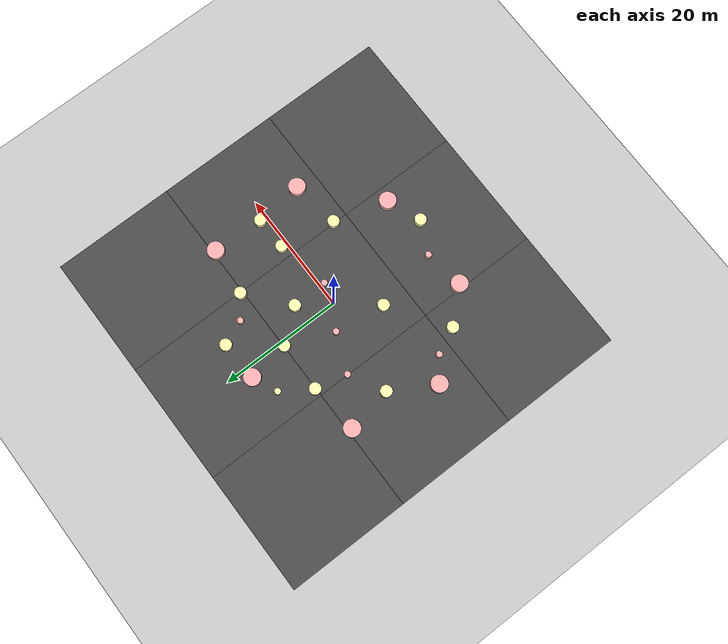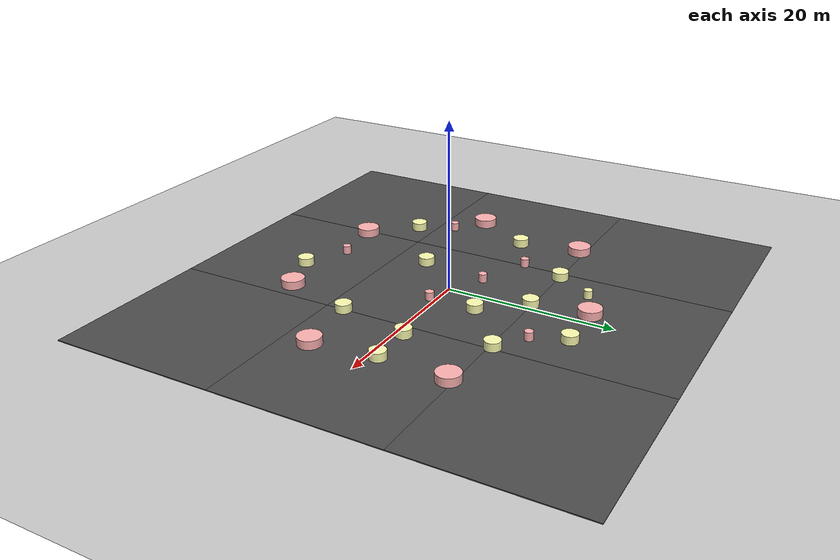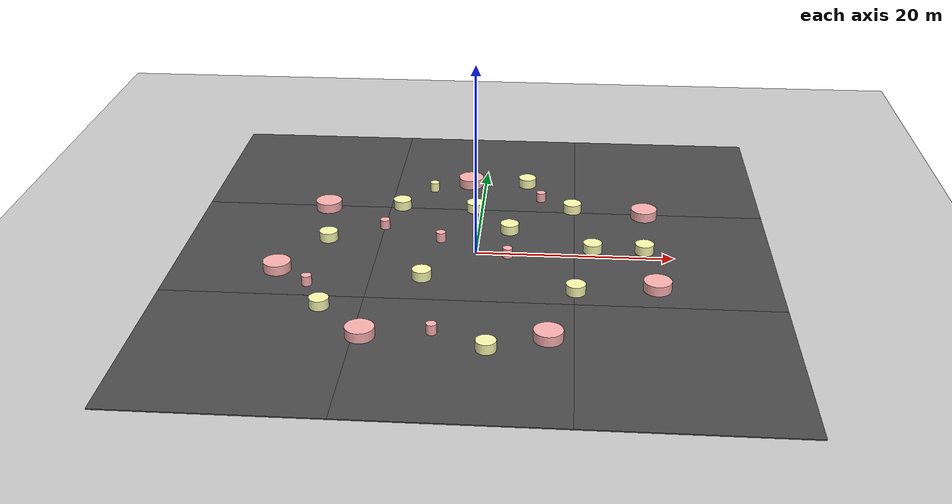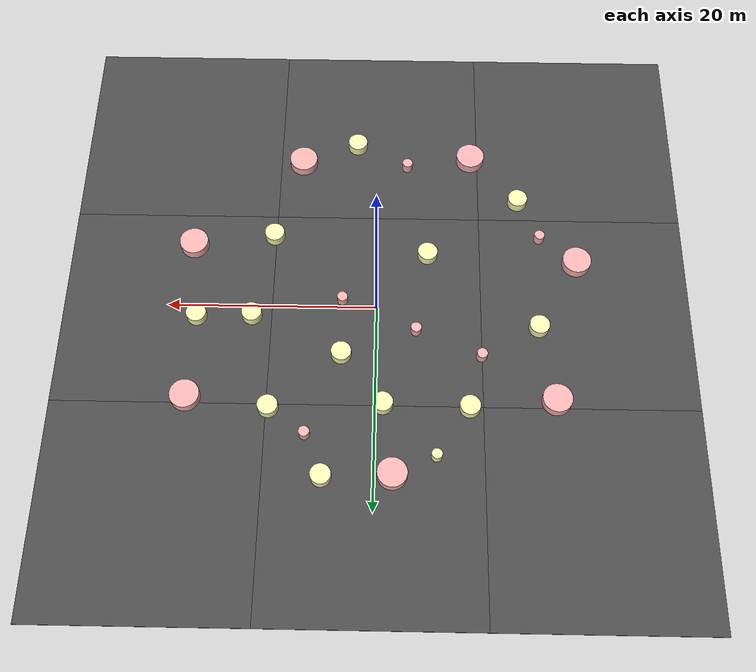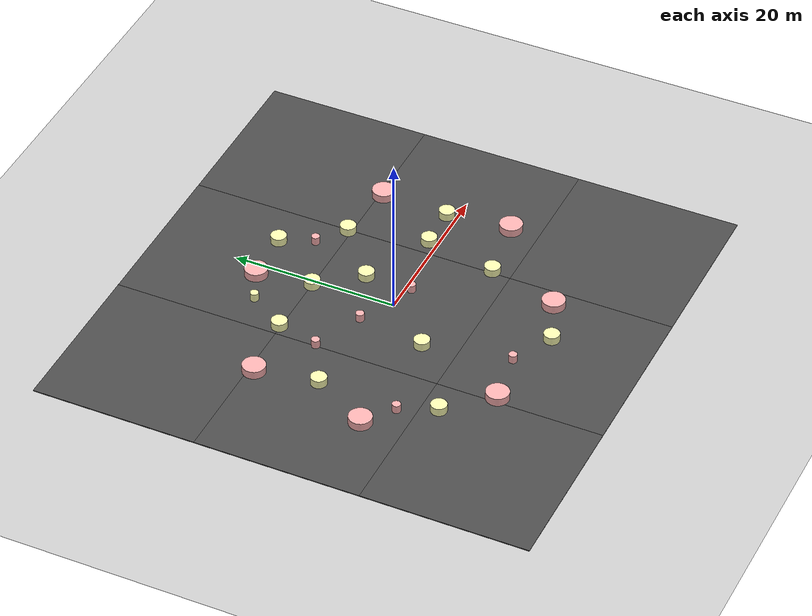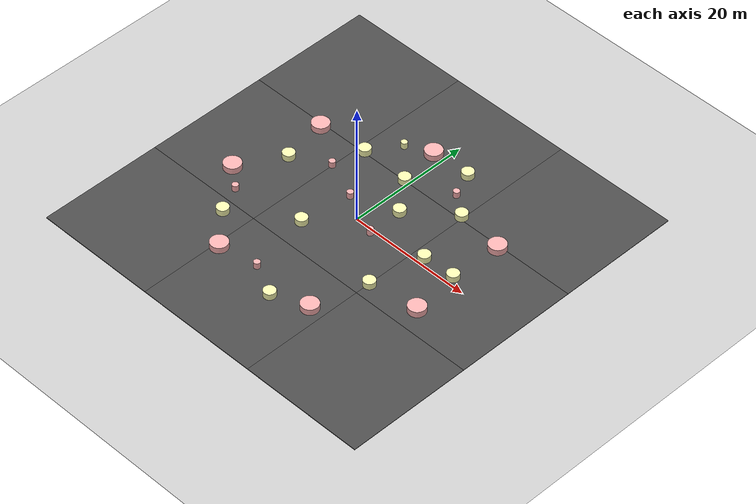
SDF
<sdf version="1.6">
 <world name="default">
  <light name="sun" type="directional">
   <pose>0 0 10 0 -0 0</pose>
   <diffuse>0.8 0.8 0.8 1</diffuse>
   <specular>0.1 0.1 0.1 1</specular>
   <attenuation>
    <range>1000</range>
    <constant>0.9</constant>
    <linear>0.01</linear>
    <quadratic>0.001</quadratic>
   </attenuation>
   <direction>-0.5 0.5 -1</direction>
  </light>
  <model name="ground_plane">
   <static>1</static>
   <link name="link">
    <collision name="collision">
     <geometry><plane><normal>0 0 1</normal><size>100 100</size></plane></geometry>
     <surface><friction><ode><mu>100</mu><mu2>50</mu2></ode></friction></surface>
    </collision>
    <visual name="visual">
     <cast_shadows>0</cast_shadows>
     <geometry><plane><normal>0 0 1</normal><size>100 100</size></plane></geometry>
     <material>
      <script><uri>file://media/materials/scripts/gazebo.material</uri><name>Gazebo/Grey</name></script>
     </material>
    </visual>
   </link>
  </model>
  <gravity>0 0 -9.8</gravity>
  <magnetic_field>6e-06 2.3e-05 -4.2e-05</magnetic_field>
  <atmosphere type="adiabatic"/>
  <physics name="default_physics" default="0" type="ode">
   <max_step_size>0.001</max_step_size>
   <real_time_factor>1</real_time_factor>
   <real_time_update_rate>1000</real_time_update_rate>
  </physics>
  <scene><ambient>0.4 0.4 0.4 1</ambient><background>0.7 0.7 0.7 1</background><shadows>1</shadows></scene>
  <spherical_coordinates>
   <surface_model>EARTH_WGS84</surface_model>
   <latitude_deg>0</latitude_deg>
   <longitude_deg>0</longitude_deg>
   <elevation>0</elevation>
   <heading_deg>0</heading_deg>
  </spherical_coordinates>
  <model name="asphalt_plane">
   <static>1</static>
   <link name="link">
    <collision name="collision"><geometry><box><size>20 20 0.1</size></box></geometry></collision>
    <visual name="visual">
     <cast_shadows>0</cast_shadows>
     <geometry><box><size>20 20 0.1</size></box></geometry>
     <material>
      <script>
       <uri>model://asphalt_plane/materials/scripts</uri>
       <uri>model://asphalt_plane/materials/textures</uri>
       <name>vrc/asphalt</name>
      </script>
     </material>
    </visual>
   </link>
  </model>
  <model name="asphalt_plane_clone">
   <static>1</static>
   <link name="link">
    <collision name="collision"><geometry><box><size>20 20 0.1</size></box></geometry></collision>
    <visual name="visual">
     <cast_shadows>0</cast_shadows>
     <geometry><box><size>20 20 0.1</size></box></geometry>
     <material>
      <script>
       <uri>model://asphalt_plane/materials/scripts</uri>
       <uri>model://asphalt_plane/materials/textures</uri>
       <name>vrc/asphalt</name>
      </script>
     </material>
    </visual>
   </link>
   <pose>-20 0 0 0 -0 0</pose>
  </model>
  <model name="asphalt_plane_clone_clone">
   <static>1</static>
   <link name="link">
    <collision name="collision"><geometry><box><size>20 20 0.1</size></box></geometry></collision>
    <visual name="visual">
     <cast_shadows>0</cast_shadows>
     <geometry><box><size>20 20 0.1</size></box></geometry>
     <material>
      <script>
       <uri>model://asphalt_plane/materials/scripts</uri>
       <uri>model://asphalt_plane/materials/textures</uri>
       <name>vrc/asphalt</name>
      </script>
     </material>
    </visual>
   </link>
   <pose>20 20 0 0 -0 0</pose>
  </model>
  <model name="asphalt_plane_clone_clone_clone">
   <static>1</static>
   <link name="link">
    <collision name="collision"><geometry><box><size>20 20 0.1</size></box></geometry></collision>
    <visual name="visual">
     <cast_shadows>0</cast_shadows>
     <geometry><box><size>20 20 0.1</size></box></geometry>
     <material>
      <script>
       <uri>model://asphalt_plane/materials/scripts</uri>
       <uri>model://asphalt_plane/materials/textures</uri>
       <name>vrc/asphalt</name>
      </script>
     </material>
    </visual>
   </link>
   <pose>0 20 0 0 -0 0</pose>
  </model>
  <model name="asphalt_plane_clone_clone_clone_0">
   <static>1</static>
   <link name="link">
    <collision name="collision"><geometry><box><size>20 20 0.1</size></box></geometry></collision>
    <visual name="visual">
     <cast_shadows>0</cast_shadows>
     <geometry><box><size>20 20 0.1</size></box></geometry>
     <material>
      <script>
       <uri>model://asphalt_plane/materials/scripts</uri>
       <uri>model://asphalt_plane/materials/textures</uri>
       <name>vrc/asphalt</name>
      </script>
     </material>
    </visual>
   </link>
   <pose>-20 20 0 0 -0 0</pose>
  </model>
  <model name="asphalt_plane_clone_clone_clone_1">
   <static>1</static>
   <link name="link">
    <collision name="collision"><geometry><box><size>20 20 0.1</size></box></geometry></collision>
    <visual name="visual">
     <cast_shadows>0</cast_shadows>
     <geometry><box><size>20 20 0.1</size></box></geometry>
     <material>
      <script>
       <uri>model://asphalt_plane/materials/scripts</uri>
       <uri>model://asphalt_plane/materials/textures</uri>
       <name>vrc/asphalt</name>
      </script>
     </material>
    </visual>
   </link>
   <pose>20 0 0 0 -0 0</pose>
  </model>
  <model name="asphalt_plane_clone_clone_clone_2">
   <static>1</static>
   <link name="link">
    <collision name="collision"><geometry><box><size>20 20 0.1</size></box></geometry></collision>
    <visual name="visual">
     <cast_shadows>0</cast_shadows>
     <geometry><box><size>20 20 0.1</size></box></geometry>
     <material>
      <script>
       <uri>model://asphalt_plane/materials/scripts</uri>
       <uri>model://asphalt_plane/materials/textures</uri>
       <name>vrc/asphalt</name>
      </script>
     </material>
    </visual>
   </link>
   <pose>20 -20 0 0 -0 0</pose>
  </model>
  <model name="asphalt_plane_clone_clone_clone_3">
   <static>1</static>
   <link name="link">
    <collision name="collision"><geometry><box><size>20 20 0.1</size></box></geometry></collision>
    <visual name="visual">
     <cast_shadows>0</cast_shadows>
     <geometry><box><size>20 20 0.1</size></box></geometry>
     <material>
      <script>
       <uri>model://asphalt_plane/materials/scripts</uri>
       <uri>model://asphalt_plane/materials/textures</uri>
       <name>vrc/asphalt</name>
      </script>
     </material>
    </visual>
   </link>
   <pose>0 -20 0 0 -0 0</pose>
  </model>
  <model name="asphalt_plane_clone_clone_clone_4">
   <static>1</static>
   <link name="link">
    <collision name="collision"><geometry><box><size>20 20 0.1</size></box></geometry></collision>
    <visual name="visual">
     <cast_shadows>0</cast_shadows>
     <geometry><box><size>20 20 0.1</size></box></geometry>
     <material>
      <script>
       <uri>model://asphalt_plane/materials/scripts</uri>
       <uri>model://asphalt_plane/materials/textures</uri>
       <name>vrc/asphalt</name>
      </script>
     </material>
    </visual>
   </link>
   <pose>-20 -20 0 0 -0 0</pose>
  </model>
  <light name="user_directional_light_0" type="directional">
   <pose>-0.142634 0.042681 1 0 -0 0</pose>
   <diffuse>0.5 0.5 0.5 1</diffuse>
   <specular>0.1 0.1 0.1 1</specular>
   <direction>0.1 0.1 -0.9</direction>
   <attenuation>
    <range>20</range>
    <constant>0.5</constant>
    <linear>0.01</linear>
    <quadratic>0.001</quadratic>
   </attenuation>
  </light>
  <model name="LandmarksColoured_1">
   <link name="link_4">
    <pose>-2.89321 -15.9613 0 0 -0 0</pose>
    <inertial>
     <mass>1</mass>
     <inertia><ixx>0.145833</ixx><ixy>0</ixy><ixz>0</ixz><iyy>0.145833</iyy><iyz>0</iyz><izz>0.125</izz></inertia>
    </inertial>
    <visual name="visual">
     <geometry><cylinder><radius>0.5</radius><length>1</length></cylinder></geometry>
     <material>
      <lighting>1</lighting>
      <script><uri>file://media/materials/scripts/gazebo.material</uri><name>Gazebo/Grey</name></script>
      <ambient>1 0.3 0.3 1</ambient>
      <diffuse>1 0.7 0.7 1</diffuse>
      <specular>1 0.01 0.01 1</specular>
      <emissive>1 0 0 1</emissive>
      <shader type="vertex"><normal_map>__default__</normal_map></shader>
     </material>
    </visual>
    <collision name="collision">
     <geometry><cylinder><radius>0.5</radius><length>1</length></cylinder></geometry>
     <surface>
      <friction>
       <ode><mu>1</mu><mu2>1</mu2><fdir1>0 0 0</fdir1><slip1>0</slip1><slip2>0</slip2></ode>
       <torsional>
        <coefficient>1</coefficient>
        <patch_radius>0</patch_radius>
        <surface_radius>0</surface_radius>
        <use_patch_radius>1</use_patch_radius>
        <ode><slip>0</slip></ode>
       </torsional>
      </friction>
      <bounce><restitution_coefficient>0</restitution_coefficient><threshold>1e+06</threshold></bounce>
      <contact>
       <collide_without_contact>0</collide_without_contact>
       <collide_without_contact_bitmask>1</collide_without_contact_bitmask>
       <collide_bitmask>1</collide_bitmask>
       <ode>
        <soft_cfm>0</soft_cfm>
        <soft_erp>0.2</soft_erp>
        <kp>1e+13</kp>
        <kd>1</kd>
        <max_vel>0.01</max_vel>
        <min_depth>0</min_depth>
       </ode>
       <bullet>
        <split_impulse>1</split_impulse>
        <split_impulse_penetration_threshold>-0.01</split_impulse_penetration_threshold>
        <soft_cfm>0</soft_cfm>
        <soft_erp>0.2</soft_erp>
        <kp>1e+13</kp>
        <kd>1</kd>
       </bullet>
      </contact>
     </surface>
    </collision>
   </link>
   <link name="link_4_clone">
    <pose>-5.38997 14.9192 -0 0 -0 0</pose>
    <inertial>
     <mass>1</mass>
     <inertia><ixx>0.145833</ixx><ixy>0</ixy><ixz>0</ixz><iyy>0.145833</iyy><iyz>0</iyz><izz>0.125</izz></inertia>
    </inertial>
    <visual name="ModelPreview_4::link_4_clone::visual_1">
     <geometry><cylinder><radius>0.5</radius><length>1</length></cylinder></geometry>
     <material>
      <lighting>1</lighting>
      <script><uri>file://media/materials/scripts/gazebo.material</uri><name>Gazebo/Grey</name></script>
      <ambient>1 1 0.3 1</ambient>
      <diffuse>1 1 0.7 1</diffuse>
      <specular>1 1 0.01 1</specular>
      <emissive>1 0 0 1</emissive>
      <shader type="vertex"><normal_map>__default__</normal_map></shader>
     </material>
    </visual>
    <visual name="visual">
     <geometry><cylinder><radius>0.5</radius><length>1</length></cylinder></geometry>
     <material>
      <lighting>1</lighting>
      <script><uri>file://media/materials/scripts/gazebo.material</uri><name>Gazebo/Grey</name></script>
      <ambient>1 1 0.3 1</ambient>
      <diffuse>1 1 0.7 1</diffuse>
      <specular>1 1 0.01 1</specular>
      <emissive>1 1 0 1</emissive>
      <shader type="vertex"><normal_map>__default__</normal_map></shader>
     </material>
    </visual>
    <collision name="collision">
     <geometry><cylinder><radius>0.5</radius><length>1</length></cylinder></geometry>
     <surface>
      <friction>
       <ode><mu>1</mu><mu2>1</mu2><fdir1>0 0 0</fdir1><slip1>0</slip1><slip2>0</slip2></ode>
       <torsional>
        <coefficient>1</coefficient>
        <patch_radius>0</patch_radius>
        <surface_radius>0</surface_radius>
        <use_patch_radius>1</use_patch_radius>
        <ode><slip>0</slip></ode>
       </torsional>
      </friction>
      <bounce><restitution_coefficient>0</restitution_coefficient><threshold>1e+06</threshold></bounce>
      <contact>
       <collide_without_contact>0</collide_without_contact>
       <collide_without_contact_bitmask>1</collide_without_contact_bitmask>
       <collide_bitmask>1</collide_bitmask>
       <ode>
        <soft_cfm>0</soft_cfm>
        <soft_erp>0.2</soft_erp>
        <kp>1e+13</kp>
        <kd>1</kd>
        <max_vel>0.01</max_vel>
        <min_depth>0</min_depth>
       </ode>
       <bullet>
        <split_impulse>1</split_impulse>
        <split_impulse_penetration_threshold>-0.01</split_impulse_penetration_threshold>
        <soft_cfm>0</soft_cfm>
        <soft_erp>0.2</soft_erp>
        <kp>1e+13</kp>
        <kd>1</kd>
       </bullet>
      </contact>
     </surface>
    </collision>
   </link>
   <link name="link_4_clone_0">
    <pose>-16.491 9.53201 -0 0 -0 0</pose>
    <inertial>
     <mass>7.6137</mass>
     <inertia><ixx>4.2575</ixx><ixy>0</ixy><ixz>0</ixz><iyy>4.2575</iyy><iyz>0</iyz><izz>7.24605</izz></inertia>
    </inertial>
    <visual name="visual">
     <geometry><cylinder><radius>1.37965</radius><length>1</length></cylinder></geometry>
     <material>
      <lighting>1</lighting>
      <script><uri>file://media/materials/scripts/gazebo.material</uri><name>Gazebo/Grey</name></script>
      <ambient>1 0.3 0.3 1</ambient>
      <diffuse>1 0.7 0.7 1</diffuse>
      <specular>1 0.01 0.01 1</specular>
      <emissive>1 0 0 1</emissive>
      <shader type="vertex"><normal_map>__default__</normal_map></shader>
     </material>
    </visual>
    <collision name="collision">
     <geometry><cylinder><radius>1.37965</radius><length>1</length></cylinder></geometry>
     <surface>
      <friction>
       <ode><mu>1</mu><mu2>1</mu2><fdir1>0 0 0</fdir1><slip1>0</slip1><slip2>0</slip2></ode>
       <torsional>
        <coefficient>1</coefficient>
        <patch_radius>0</patch_radius>
        <surface_radius>0</surface_radius>
        <use_patch_radius>1</use_patch_radius>
        <ode><slip>0</slip></ode>
       </torsional>
      </friction>
      <bounce><restitution_coefficient>0</restitution_coefficient><threshold>1e+06</threshold></bounce>
      <contact>
       <collide_without_contact>0</collide_without_contact>
       <collide_without_contact_bitmask>1</collide_without_contact_bitmask>
       <collide_bitmask>1</collide_bitmask>
       <ode>
        <soft_cfm>0</soft_cfm>
        <soft_erp>0.2</soft_erp>
        <kp>1e+13</kp>
        <kd>1</kd>
        <max_vel>0.01</max_vel>
        <min_depth>0</min_depth>
       </ode>
       <bullet>
        <split_impulse>1</split_impulse>
        <split_impulse_penetration_threshold>-0.01</split_impulse_penetration_threshold>
        <soft_cfm>0</soft_cfm>
        <soft_erp>0.2</soft_erp>
        <kp>1e+13</kp>
        <kd>1</kd>
       </bullet>
      </contact>
     </surface>
    </collision>
   </link>
   <link name="link_4_clone_0_clone">
    <pose>-19.3072 -4.8348 -0 0 -0 0</pose>
    <inertial>
     <mass>7.6137</mass>
     <inertia><ixx>4.2575</ixx><ixy>0</ixy><ixz>0</ixz><iyy>4.2575</iyy><iyz>0</iyz><izz>7.24605</izz></inertia>
    </inertial>
    <visual name="visual">
     <geometry><cylinder><radius>1.37965</radius><length>1</length></cylinder></geometry>
     <material>
      <lighting>1</lighting>
      <script><uri>file://media/materials/scripts/gazebo.material</uri><name>Gazebo/Grey</name></script>
      <ambient>1 0.3 0.3 1</ambient>
      <diffuse>1 0.7 0.7 1</diffuse>
      <specular>1 0.01 0.01 1</specular>
      <emissive>1 0 0 1</emissive>
      <shader type="vertex"><normal_map>__default__</normal_map></shader>
     </material>
    </visual>
    <collision name="collision">
     <geometry><cylinder><radius>1.37965</radius><length>1</length></cylinder></geometry>
     <surface>
      <friction>
       <ode><mu>1</mu><mu2>1</mu2><fdir1>0 0 0</fdir1><slip1>0</slip1><slip2>0</slip2></ode>
       <torsional>
        <coefficient>1</coefficient>
        <patch_radius>0</patch_radius>
        <surface_radius>0</surface_radius>
        <use_patch_radius>1</use_patch_radius>
        <ode><slip>0</slip></ode>
       </torsional>
      </friction>
      <bounce><restitution_coefficient>0</restitution_coefficient><threshold>1e+06</threshold></bounce>
      <contact>
       <collide_without_contact>0</collide_without_contact>
       <collide_without_contact_bitmask>1</collide_without_contact_bitmask>
       <collide_bitmask>1</collide_bitmask>
       <ode>
        <soft_cfm>0</soft_cfm>
        <soft_erp>0.2</soft_erp>
        <kp>1e+13</kp>
        <kd>1</kd>
        <max_vel>0.01</max_vel>
        <min_depth>0</min_depth>
       </ode>
       <bullet>
        <split_impulse>1</split_impulse>
        <split_impulse_penetration_threshold>-0.01</split_impulse_penetration_threshold>
        <soft_cfm>0</soft_cfm>
        <soft_erp>0.2</soft_erp>
        <kp>1e+13</kp>
        <kd>1</kd>
       </bullet>
      </contact>
     </surface>
    </collision>
   </link>
   <link name="link_4_clone_0_clone_0">
    <pose>18.101 -6.65934 0 0 -0 0</pose>
    <inertial>
     <mass>7.6137</mass>
     <inertia><ixx>4.2575</ixx><ixy>0</ixy><ixz>0</ixz><iyy>4.2575</iyy><iyz>0</iyz><izz>7.24605</izz></inertia>
    </inertial>
    <visual name="visual">
     <geometry><cylinder><radius>1.37965</radius><length>1</length></cylinder></geometry>
     <material>
      <lighting>1</lighting>
      <script><uri>file://media/materials/scripts/gazebo.material</uri><name>Gazebo/Grey</name></script>
      <ambient>1 0.3 0.3 1</ambient>
      <diffuse>1 0.7 0.7 1</diffuse>
      <specular>1 0.01 0.01 1</specular>
      <emissive>1 0 0 1</emissive>
      <shader type="vertex"><normal_map>__default__</normal_map></shader>
     </material>
    </visual>
    <collision name="collision">
     <geometry><cylinder><radius>1.37965</radius><length>1</length></cylinder></geometry>
     <surface>
      <friction>
       <ode><mu>1</mu><mu2>1</mu2><fdir1>0 0 0</fdir1><slip1>0</slip1><slip2>0</slip2></ode>
       <torsional>
        <coefficient>1</coefficient>
        <patch_radius>0</patch_radius>
        <surface_radius>0</surface_radius>
        <use_patch_radius>1</use_patch_radius>
        <ode><slip>0</slip></ode>
       </torsional>
      </friction>
      <bounce><restitution_coefficient>0</restitution_coefficient><threshold>1e+06</threshold></bounce>
      <contact>
       <collide_without_contact>0</collide_without_contact>
       <collide_without_contact_bitmask>1</collide_without_contact_bitmask>
       <collide_bitmask>1</collide_bitmask>
       <ode>
        <soft_cfm>0</soft_cfm>
        <soft_erp>0.2</soft_erp>
        <kp>1e+13</kp>
        <kd>1</kd>
        <max_vel>0.01</max_vel>
        <min_depth>0</min_depth>
       </ode>
       <bullet>
        <split_impulse>1</split_impulse>
        <split_impulse_penetration_threshold>-0.01</split_impulse_penetration_threshold>
        <soft_cfm>0</soft_cfm>
        <soft_erp>0.2</soft_erp>
        <kp>1e+13</kp>
        <kd>1</kd>
       </bullet>
      </contact>
     </surface>
    </collision>
   </link>
   <link name="link_4_clone_0_clone_1">
    <pose>17.6574 9.38126 0 0 -0 0</pose>
    <inertial>
     <mass>7.6137</mass>
     <inertia><ixx>4.2575</ixx><ixy>0</ixy><ixz>0</ixz><iyy>4.2575</iyy><iyz>0</iyz><izz>7.24605</izz></inertia>
    </inertial>
    <visual name="visual">
     <geometry><cylinder><radius>1.37965</radius><length>1</length></cylinder></geometry>
     <material>
      <lighting>1</lighting>
      <script><uri>file://media/materials/scripts/gazebo.material</uri><name>Gazebo/Grey</name></script>
      <ambient>1 0.3 0.3 1</ambient>
      <diffuse>1 0.7 0.7 1</diffuse>
      <specular>1 0.01 0.01 1</specular>
      <emissive>1 0 0 1</emissive>
      <shader type="vertex"><normal_map>__default__</normal_map></shader>
     </material>
    </visual>
    <collision name="collision">
     <geometry><cylinder><radius>1.37965</radius><length>1</length></cylinder></geometry>
     <surface>
      <friction>
       <ode><mu>1</mu><mu2>1</mu2><fdir1>0 0 0</fdir1><slip1>0</slip1><slip2>0</slip2></ode>
       <torsional>
        <coefficient>1</coefficient>
        <patch_radius>0</patch_radius>
        <surface_radius>0</surface_radius>
        <use_patch_radius>1</use_patch_radius>
        <ode><slip>0</slip></ode>
       </torsional>
      </friction>
      <bounce><restitution_coefficient>0</restitution_coefficient><threshold>1e+06</threshold></bounce>
      <contact>
       <collide_without_contact>0</collide_without_contact>
       <collide_without_contact_bitmask>1</collide_without_contact_bitmask>
       <collide_bitmask>1</collide_bitmask>
       <ode>
        <soft_cfm>0</soft_cfm>
        <soft_erp>0.2</soft_erp>
        <kp>1e+13</kp>
        <kd>1</kd>
        <max_vel>0.01</max_vel>
        <min_depth>0</min_depth>
       </ode>
       <bullet>
        <split_impulse>1</split_impulse>
        <split_impulse_penetration_threshold>-0.01</split_impulse_penetration_threshold>
        <soft_cfm>0</soft_cfm>
        <soft_erp>0.2</soft_erp>
        <kp>1e+13</kp>
        <kd>1</kd>
       </bullet>
      </contact>
     </surface>
    </collision>
   </link>
   <link name="link_4_clone_0_clone_2">
    <pose>-1.39165 16.6645 -0 0 -0 0</pose>
    <inertial>
     <mass>7.6137</mass>
     <inertia><ixx>4.2575</ixx><ixy>0</ixy><ixz>0</ixz><iyy>4.2575</iyy><iyz>0</iyz><izz>7.24605</izz></inertia>
    </inertial>
    <visual name="visual">
     <geometry><cylinder><radius>1.37965</radius><length>1</length></cylinder></geometry>
     <material>
      <lighting>1</lighting>
      <script><uri>file://media/materials/scripts/gazebo.material</uri><name>Gazebo/Grey</name></script>
      <ambient>1 0.3 0.3 1</ambient>
      <diffuse>1 0.7 0.7 1</diffuse>
      <specular>1 0.01 0.01 1</specular>
      <emissive>1 0 0 1</emissive>
      <shader type="vertex"><normal_map>__default__</normal_map></shader>
     </material>
    </visual>
    <collision name="collision">
     <geometry><cylinder><radius>1.37965</radius><length>1</length></cylinder></geometry>
     <surface>
      <friction>
       <ode><mu>1</mu><mu2>1</mu2><fdir1>0 0 0</fdir1><slip1>0</slip1><slip2>0</slip2></ode>
       <torsional>
        <coefficient>1</coefficient>
        <patch_radius>0</patch_radius>
        <surface_radius>0</surface_radius>
        <use_patch_radius>1</use_patch_radius>
        <ode><slip>0</slip></ode>
       </torsional>
      </friction>
      <bounce><restitution_coefficient>0</restitution_coefficient><threshold>1e+06</threshold></bounce>
      <contact>
       <collide_without_contact>0</collide_without_contact>
       <collide_without_contact_bitmask>1</collide_without_contact_bitmask>
       <collide_bitmask>1</collide_bitmask>
       <ode>
        <soft_cfm>0</soft_cfm>
        <soft_erp>0.2</soft_erp>
        <kp>1e+13</kp>
        <kd>1</kd>
        <max_vel>0.01</max_vel>
        <min_depth>0</min_depth>
       </ode>
       <bullet>
        <split_impulse>1</split_impulse>
        <split_impulse_penetration_threshold>-0.01</split_impulse_penetration_threshold>
        <soft_cfm>0</soft_cfm>
        <soft_erp>0.2</soft_erp>
        <kp>1e+13</kp>
        <kd>1</kd>
       </bullet>
      </contact>
     </surface>
    </collision>
   </link>
   <link name="link_4_clone_0_clone_clone">
    <pose>-9.29686 -16.885 0 0 -0 0</pose>
    <inertial>
     <mass>7.6137</mass>
     <inertia><ixx>4.2575</ixx><ixy>0</ixy><ixz>0</ixz><iyy>4.2575</iyy><iyz>0</iyz><izz>7.24605</izz></inertia>
    </inertial>
    <visual name="visual">
     <geometry><cylinder><radius>1.37965</radius><length>1</length></cylinder></geometry>
     <material>
      <lighting>1</lighting>
      <script><uri>file://media/materials/scripts/gazebo.material</uri><name>Gazebo/Grey</name></script>
      <ambient>1 0.3 0.3 1</ambient>
      <diffuse>1 0.7 0.7 1</diffuse>
      <specular>1 0.01 0.01 1</specular>
      <emissive>1 0 0 1</emissive>
      <shader type="vertex"><normal_map>__default__</normal_map></shader>
     </material>
    </visual>
    <collision name="collision">
     <geometry><cylinder><radius>1.37965</radius><length>1</length></cylinder></geometry>
     <surface>
      <friction>
       <ode><mu>1</mu><mu2>1</mu2><fdir1>0 0 0</fdir1><slip1>0</slip1><slip2>0</slip2></ode>
       <torsional>
        <coefficient>1</coefficient>
        <patch_radius>0</patch_radius>
        <surface_radius>0</surface_radius>
        <use_patch_radius>1</use_patch_radius>
        <ode><slip>0</slip></ode>
       </torsional>
      </friction>
      <bounce><restitution_coefficient>0</restitution_coefficient><threshold>1e+06</threshold></bounce>
      <contact>
       <collide_without_contact>0</collide_without_contact>
       <collide_without_contact_bitmask>1</collide_without_contact_bitmask>
       <collide_bitmask>1</collide_bitmask>
       <ode>
        <soft_cfm>0</soft_cfm>
        <soft_erp>0.2</soft_erp>
        <kp>1e+13</kp>
        <kd>1</kd>
        <max_vel>0.01</max_vel>
        <min_depth>0</min_depth>
       </ode>
       <bullet>
        <split_impulse>1</split_impulse>
        <split_impulse_penetration_threshold>-0.01</split_impulse_penetration_threshold>
        <soft_cfm>0</soft_cfm>
        <soft_erp>0.2</soft_erp>
        <kp>1e+13</kp>
        <kd>1</kd>
       </bullet>
      </contact>
     </surface>
    </collision>
   </link>
   <link name="link_4_clone_0_clone_clone_0">
    <pose>7.70314 -16.4099 0 0 -0 0</pose>
    <inertial>
     <mass>7.6137</mass>
     <inertia><ixx>4.2575</ixx><ixy>0</ixy><ixz>0</ixz><iyy>4.2575</iyy><iyz>0</iyz><izz>7.24605</izz></inertia>
    </inertial>
    <visual name="visual">
     <geometry><cylinder><radius>1.37965</radius><length>1</length></cylinder></geometry>
     <material>
      <lighting>1</lighting>
      <script><uri>file://media/materials/scripts/gazebo.material</uri><name>Gazebo/Grey</name></script>
      <ambient>1 0.3 0.3 1</ambient>
      <diffuse>1 0.7 0.7 1</diffuse>
      <specular>1 0.01 0.01 1</specular>
      <emissive>1 0 0 1</emissive>
      <shader type="vertex"><normal_map>__default__</normal_map></shader>
     </material>
    </visual>
    <collision name="collision">
     <geometry><cylinder><radius>1.37965</radius><length>1</length></cylinder></geometry>
     <surface>
      <friction>
       <ode><mu>1</mu><mu2>1</mu2><fdir1>0 0 0</fdir1><slip1>0</slip1><slip2>0</slip2></ode>
       <torsional>
        <coefficient>1</coefficient>
        <patch_radius>0</patch_radius>
        <surface_radius>0</surface_radius>
        <use_patch_radius>1</use_patch_radius>
        <ode><slip>0</slip></ode>
       </torsional>
      </friction>
      <bounce><restitution_coefficient>0</restitution_coefficient><threshold>1e+06</threshold></bounce>
      <contact>
       <collide_without_contact>0</collide_without_contact>
       <collide_without_contact_bitmask>1</collide_without_contact_bitmask>
       <collide_bitmask>1</collide_bitmask>
       <ode>
        <soft_cfm>0</soft_cfm>
        <soft_erp>0.2</soft_erp>
        <kp>1e+13</kp>
        <kd>1</kd>
        <max_vel>0.01</max_vel>
        <min_depth>0</min_depth>
       </ode>
       <bullet>
        <split_impulse>1</split_impulse>
        <split_impulse_penetration_threshold>-0.01</split_impulse_penetration_threshold>
        <soft_cfm>0</soft_cfm>
        <soft_erp>0.2</soft_erp>
        <kp>1e+13</kp>
        <kd>1</kd>
       </bullet>
      </contact>
     </surface>
    </collision>
   </link>
   <link name="link_4_clone_1">
    <pose>-15.8394 -7.60505 1.4e-05 0 -0 0</pose>
    <inertial>
     <mass>1</mass>
     <inertia><ixx>0.145833</ixx><ixy>0</ixy><ixz>0</ixz><iyy>0.145833</iyy><iyz>0</iyz><izz>0.125</izz></inertia>
    </inertial>
    <visual name="visual">
     <geometry><cylinder><radius>0.5</radius><length>1</length></cylinder></geometry>
     <material>
      <lighting>1</lighting>
      <script><uri>file://media/materials/scripts/gazebo.material</uri><name>Gazebo/Grey</name></script>
      <ambient>1 0.3 0.3 1</ambient>
      <diffuse>1 0.7 0.7 1</diffuse>
      <specular>1 0.01 0.01 1</specular>
      <emissive>1 0 0 1</emissive>
      <shader type="vertex"><normal_map>__default__</normal_map></shader>
     </material>
    </visual>
    <collision name="collision">
     <geometry><cylinder><radius>0.5</radius><length>1</length></cylinder></geometry>
     <surface>
      <friction>
       <ode><mu>1</mu><mu2>1</mu2><fdir1>0 0 0</fdir1><slip1>0</slip1><slip2>0</slip2></ode>
       <torsional>
        <coefficient>1</coefficient>
        <patch_radius>0</patch_radius>
        <surface_radius>0</surface_radius>
        <use_patch_radius>1</use_patch_radius>
        <ode><slip>0</slip></ode>
       </torsional>
      </friction>
      <bounce><restitution_coefficient>0</restitution_coefficient><threshold>1e+06</threshold></bounce>
      <contact>
       <collide_without_contact>0</collide_without_contact>
       <collide_without_contact_bitmask>1</collide_without_contact_bitmask>
       <collide_bitmask>1</collide_bitmask>
       <ode>
        <soft_cfm>0</soft_cfm>
        <soft_erp>0.2</soft_erp>
        <kp>1e+13</kp>
        <kd>1</kd>
        <max_vel>0.01</max_vel>
        <min_depth>0</min_depth>
       </ode>
       <bullet>
        <split_impulse>1</split_impulse>
        <split_impulse_penetration_threshold>-0.01</split_impulse_penetration_threshold>
        <soft_cfm>0</soft_cfm>
        <soft_erp>0.2</soft_erp>
        <kp>1e+13</kp>
        <kd>1</kd>
       </bullet>
      </contact>
     </surface>
    </collision>
   </link>
   <link name="link_4_clone_2">
    <pose>3.40156 -0.6744 1e-05 0 -0 0</pose>
    <inertial>
     <mass>1</mass>
     <inertia><ixx>0.145833</ixx><ixy>0</ixy><ixz>0</ixz><iyy>0.145833</iyy><iyz>0</iyz><izz>0.125</izz></inertia>
    </inertial>
    <visual name="visual">
     <geometry><cylinder><radius>0.5</radius><length>1</length></cylinder></geometry>
     <material>
      <lighting>1</lighting>
      <script><uri>file://media/materials/scripts/gazebo.material</uri><name>Gazebo/Grey</name></script>
      <ambient>1 0.3 0.3 1</ambient>
      <diffuse>1 0.7 0.7 1</diffuse>
      <specular>1 0.01 0.01 1</specular>
      <emissive>1 0 0 1</emissive>
      <shader type="vertex"><normal_map>__default__</normal_map></shader>
     </material>
    </visual>
    <collision name="collision">
     <geometry><cylinder><radius>0.5</radius><length>1</length></cylinder></geometry>
     <surface>
      <friction>
       <ode><mu>1</mu><mu2>1</mu2><fdir1>0 0 0</fdir1><slip1>0</slip1><slip2>0</slip2></ode>
       <torsional>
        <coefficient>1</coefficient>
        <patch_radius>0</patch_radius>
        <surface_radius>0</surface_radius>
        <use_patch_radius>1</use_patch_radius>
        <ode><slip>0</slip></ode>
       </torsional>
      </friction>
      <bounce><restitution_coefficient>0</restitution_coefficient><threshold>1e+06</threshold></bounce>
      <contact>
       <collide_without_contact>0</collide_without_contact>
       <collide_without_contact_bitmask>1</collide_without_contact_bitmask>
       <collide_bitmask>1</collide_bitmask>
       <ode>
        <soft_cfm>0</soft_cfm>
        <soft_erp>0.2</soft_erp>
        <kp>1e+13</kp>
        <kd>1</kd>
        <max_vel>0.01</max_vel>
        <min_depth>0</min_depth>
       </ode>
       <bullet>
        <split_impulse>1</split_impulse>
        <split_impulse_penetration_threshold>-0.01</split_impulse_penetration_threshold>
        <soft_cfm>0</soft_cfm>
        <soft_erp>0.2</soft_erp>
        <kp>1e+13</kp>
        <kd>1</kd>
       </bullet>
      </contact>
     </surface>
    </collision>
   </link>
   <link name="link_4_clone_3">
    <pose>6.57429 12.9229 1.5e-05 0 -0 0</pose>
    <inertial>
     <mass>1</mass>
     <inertia><ixx>0.145833</ixx><ixy>0</ixy><ixz>0</ixz><iyy>0.145833</iyy><iyz>0</iyz><izz>0.125</izz></inertia>
    </inertial>
    <visual name="visual">
     <geometry><cylinder><radius>0.5</radius><length>1</length></cylinder></geometry>
     <material>
      <lighting>1</lighting>
      <script><uri>file://media/materials/scripts/gazebo.material</uri><name>Gazebo/Grey</name></script>
      <ambient>1 0.3 0.3 1</ambient>
      <diffuse>1 0.7 0.7 1</diffuse>
      <specular>1 0.01 0.01 1</specular>
      <emissive>1 0 0 1</emissive>
      <shader type="vertex"><normal_map>__default__</normal_map></shader>
     </material>
    </visual>
    <collision name="collision">
     <geometry><cylinder><radius>0.5</radius><length>1</length></cylinder></geometry>
     <surface>
      <friction>
       <ode><mu>1</mu><mu2>1</mu2><fdir1>0 0 0</fdir1><slip1>0</slip1><slip2>0</slip2></ode>
       <torsional>
        <coefficient>1</coefficient>
        <patch_radius>0</patch_radius>
        <surface_radius>0</surface_radius>
        <use_patch_radius>1</use_patch_radius>
        <ode><slip>0</slip></ode>
       </torsional>
      </friction>
      <bounce><restitution_coefficient>0</restitution_coefficient><threshold>1e+06</threshold></bounce>
      <contact>
       <collide_without_contact>0</collide_without_contact>
       <collide_without_contact_bitmask>1</collide_without_contact_bitmask>
       <collide_bitmask>1</collide_bitmask>
       <ode>
        <soft_cfm>0</soft_cfm>
        <soft_erp>0.2</soft_erp>
        <kp>1e+13</kp>
        <kd>1</kd>
        <max_vel>0.01</max_vel>
        <min_depth>0</min_depth>
       </ode>
       <bullet>
        <split_impulse>1</split_impulse>
        <split_impulse_penetration_threshold>-0.01</split_impulse_penetration_threshold>
        <soft_cfm>0</soft_cfm>
        <soft_erp>0.2</soft_erp>
        <kp>1e+13</kp>
        <kd>1</kd>
       </bullet>
      </contact>
     </surface>
    </collision>
   </link>
   <link name="link_4_clone_4">
    <pose>-3.62741 2.51345 -8e-06 0 -0 0</pose>
    <inertial>
     <mass>1</mass>
     <inertia><ixx>0.145833</ixx><ixy>0</ixy><ixz>0</ixz><iyy>0.145833</iyy><iyz>0</iyz><izz>0.125</izz></inertia>
    </inertial>
    <visual name="visual">
     <geometry><cylinder><radius>0.5</radius><length>1</length></cylinder></geometry>
     <material>
      <lighting>1</lighting>
      <script><uri>file://media/materials/scripts/gazebo.material</uri><name>Gazebo/Grey</name></script>
      <ambient>1 0.3 0.3 1</ambient>
      <diffuse>1 0.7 0.7 1</diffuse>
      <specular>1 0.01 0.01 1</specular>
      <emissive>1 0 0 1</emissive>
      <shader type="vertex"><normal_map>__default__</normal_map></shader>
     </material>
    </visual>
    <collision name="collision">
     <geometry><cylinder><radius>0.5</radius><length>1</length></cylinder></geometry>
     <surface>
      <friction>
       <ode><mu>1</mu><mu2>1</mu2><fdir1>0 0 0</fdir1><slip1>0</slip1><slip2>0</slip2></ode>
       <torsional>
        <coefficient>1</coefficient>
        <patch_radius>0</patch_radius>
        <surface_radius>0</surface_radius>
        <use_patch_radius>1</use_patch_radius>
        <ode><slip>0</slip></ode>
       </torsional>
      </friction>
      <bounce><restitution_coefficient>0</restitution_coefficient><threshold>1e+06</threshold></bounce>
      <contact>
       <collide_without_contact>0</collide_without_contact>
       <collide_without_contact_bitmask>1</collide_without_contact_bitmask>
       <collide_bitmask>1</collide_bitmask>
       <ode>
        <soft_cfm>0</soft_cfm>
        <soft_erp>0.2</soft_erp>
        <kp>1e+13</kp>
        <kd>1</kd>
        <max_vel>0.01</max_vel>
        <min_depth>0</min_depth>
       </ode>
       <bullet>
        <split_impulse>1</split_impulse>
        <split_impulse_penetration_threshold>-0.01</split_impulse_penetration_threshold>
        <soft_cfm>0</soft_cfm>
        <soft_erp>0.2</soft_erp>
        <kp>1e+13</kp>
        <kd>1</kd>
       </bullet>
      </contact>
     </surface>
    </collision>
   </link>
   <link name="link_4_clone_5">
    <pose>-9.77094 5.13198 1.4e-05 0 -0 0</pose>
    <inertial>
     <mass>1</mass>
     <inertia><ixx>0.145833</ixx><ixy>0</ixy><ixz>0</ixz><iyy>0.145833</iyy><iyz>0</iyz><izz>0.125</izz></inertia>
    </inertial>
    <visual name="visual">
     <geometry><cylinder><radius>0.5</radius><length>1</length></cylinder></geometry>
     <material>
      <lighting>1</lighting>
      <script><uri>file://media/materials/scripts/gazebo.material</uri><name>Gazebo/Grey</name></script>
      <ambient>1 0.3 0.3 1</ambient>
      <diffuse>1 0.7 0.7 1</diffuse>
      <specular>1 0.01 0.01 1</specular>
      <emissive>1 0 0 1</emissive>
      <shader type="vertex"><normal_map>__default__</normal_map></shader>
     </material>
    </visual>
    <collision name="collision">
     <geometry><cylinder><radius>0.5</radius><length>1</length></cylinder></geometry>
     <surface>
      <friction>
       <ode><mu>1</mu><mu2>1</mu2><fdir1>0 0 0</fdir1><slip1>0</slip1><slip2>0</slip2></ode>
       <torsional>
        <coefficient>1</coefficient>
        <patch_radius>0</patch_radius>
        <surface_radius>0</surface_radius>
        <use_patch_radius>1</use_patch_radius>
        <ode><slip>0</slip></ode>
       </torsional>
      </friction>
      <bounce><restitution_coefficient>0</restitution_coefficient><threshold>1e+06</threshold></bounce>
      <contact>
       <collide_without_contact>0</collide_without_contact>
       <collide_without_contact_bitmask>1</collide_without_contact_bitmask>
       <collide_bitmask>1</collide_bitmask>
       <ode>
        <soft_cfm>0</soft_cfm>
        <soft_erp>0.2</soft_erp>
        <kp>1e+13</kp>
        <kd>1</kd>
        <max_vel>0.01</max_vel>
        <min_depth>0</min_depth>
       </ode>
       <bullet>
        <split_impulse>1</split_impulse>
        <split_impulse_penetration_threshold>-0.01</split_impulse_penetration_threshold>
        <soft_cfm>0</soft_cfm>
        <soft_erp>0.2</soft_erp>
        <kp>1e+13</kp>
        <kd>1</kd>
       </bullet>
      </contact>
     </surface>
    </collision>
   </link>
   <link name="link_4_clone_clone">
    <pose>10.2323 -7.72786 0 0 -0 0</pose>
    <inertial>
     <mass>3.64615</mass>
     <inertia><ixx>1.13475</ixx><ixy>0</ixy><ixz>0</ixz><iyy>1.13475</iyy><iyz>0</iyz><izz>1.6618</izz></inertia>
    </inertial>
    <visual name="visual_1">
     <geometry><cylinder><radius>0.954744</radius><length>1</length></cylinder></geometry>
     <material>
      <lighting>1</lighting>
      <script><uri>file://media/materials/scripts/gazebo.material</uri><name>Gazebo/Grey</name></script>
      <ambient>1 1 0.3 1</ambient>
      <diffuse>1 1 0.7 1</diffuse>
      <specular>1 1 0.01 1</specular>
      <emissive>1 0 0 1</emissive>
      <shader type="vertex"><normal_map>__default__</normal_map></shader>
     </material>
    </visual>
    <visual name="visual">
     <geometry><cylinder><radius>0.954744</radius><length>1</length></cylinder></geometry>
     <material>
      <lighting>1</lighting>
      <script><uri>file://media/materials/scripts/gazebo.material</uri><name>Gazebo/Grey</name></script>
      <ambient>1 1 0.3 1</ambient>
      <diffuse>1 1 0.7 1</diffuse>
      <specular>1 1 0.01 1</specular>
      <emissive>1 1 0 1</emissive>
      <shader type="vertex"><normal_map>__default__</normal_map></shader>
     </material>
    </visual>
    <collision name="collision">
     <geometry><cylinder><radius>0.954744</radius><length>1</length></cylinder></geometry>
     <surface>
      <friction>
       <ode><mu>1</mu><mu2>1</mu2><fdir1>0 0 0</fdir1><slip1>0</slip1><slip2>0</slip2></ode>
       <torsional>
        <coefficient>1</coefficient>
        <patch_radius>0</patch_radius>
        <surface_radius>0</surface_radius>
        <use_patch_radius>1</use_patch_radius>
        <ode><slip>0</slip></ode>
       </torsional>
      </friction>
      <bounce><restitution_coefficient>0</restitution_coefficient><threshold>1e+06</threshold></bounce>
      <contact>
       <collide_without_contact>0</collide_without_contact>
       <collide_without_contact_bitmask>1</collide_without_contact_bitmask>
       <collide_bitmask>1</collide_bitmask>
       <ode>
        <soft_cfm>0</soft_cfm>
        <soft_erp>0.2</soft_erp>
        <kp>1e+13</kp>
        <kd>1</kd>
        <max_vel>0.01</max_vel>
        <min_depth>0</min_depth>
       </ode>
       <bullet>
        <split_impulse>1</split_impulse>
        <split_impulse_penetration_threshold>-0.01</split_impulse_penetration_threshold>
        <soft_cfm>0</soft_cfm>
        <soft_erp>0.2</soft_erp>
        <kp>1e+13</kp>
        <kd>1</kd>
       </bullet>
      </contact>
     </surface>
    </collision>
   </link>
   <link name="link_4_clone_clone_clone">
    <pose>-13.8953 -11.8511 -1e-06 0 -0 0</pose>
    <inertial>
     <mass>3.64615</mass>
     <inertia><ixx>1.13475</ixx><ixy>0</ixy><ixz>0</ixz><iyy>1.13475</iyy><iyz>0</iyz><izz>1.6618</izz></inertia>
    </inertial>
    <visual name="visual_1">
     <geometry><cylinder><radius>0.954744</radius><length>1</length></cylinder></geometry>
     <material>
      <lighting>1</lighting>
      <script><uri>file://media/materials/scripts/gazebo.material</uri><name>Gazebo/Grey</name></script>
      <ambient>1 1 0.3 1</ambient>
      <diffuse>1 1 0.7 1</diffuse>
      <specular>1 1 0.01 1</specular>
      <emissive>1 0 0 1</emissive>
      <shader type="vertex"><normal_map>__default__</normal_map></shader>
     </material>
    </visual>
    <visual name="visual">
     <geometry><cylinder><radius>0.954744</radius><length>1</length></cylinder></geometry>
     <material>
      <lighting>1</lighting>
      <script><uri>file://media/materials/scripts/gazebo.material</uri><name>Gazebo/Grey</name></script>
      <ambient>1 1 0.3 1</ambient>
      <diffuse>1 1 0.7 1</diffuse>
      <specular>1 1 0.01 1</specular>
      <emissive>1 1 0 1</emissive>
      <shader type="vertex"><normal_map>__default__</normal_map></shader>
     </material>
    </visual>
    <collision name="collision">
     <geometry><cylinder><radius>0.954744</radius><length>1</length></cylinder></geometry>
     <surface>
      <friction>
       <ode><mu>1</mu><mu2>1</mu2><fdir1>0 0 0</fdir1><slip1>0</slip1><slip2>0</slip2></ode>
       <torsional>
        <coefficient>1</coefficient>
        <patch_radius>0</patch_radius>
        <surface_radius>0</surface_radius>
        <use_patch_radius>1</use_patch_radius>
        <ode><slip>0</slip></ode>
       </torsional>
      </friction>
      <bounce><restitution_coefficient>0</restitution_coefficient><threshold>1e+06</threshold></bounce>
      <contact>
       <collide_without_contact>0</collide_without_contact>
       <collide_without_contact_bitmask>1</collide_without_contact_bitmask>
       <collide_bitmask>1</collide_bitmask>
       <ode>
        <soft_cfm>0</soft_cfm>
        <soft_erp>0.2</soft_erp>
        <kp>1e+13</kp>
        <kd>1</kd>
        <max_vel>0.01</max_vel>
        <min_depth>0</min_depth>
       </ode>
       <bullet>
        <split_impulse>1</split_impulse>
        <split_impulse_penetration_threshold>-0.01</split_impulse_penetration_threshold>
        <soft_cfm>0</soft_cfm>
        <soft_erp>0.2</soft_erp>
        <kp>1e+13</kp>
        <kd>1</kd>
       </bullet>
      </contact>
     </surface>
    </collision>
   </link>
   <link name="link_4_clone_clone_clone_0">
    <pose>9.99975 10.3839 0 0 -0 0</pose>
    <inertial>
     <mass>3.64615</mass>
     <inertia><ixx>1.13475</ixx><ixy>0</ixy><ixz>0</ixz><iyy>1.13475</iyy><iyz>0</iyz><izz>1.6618</izz></inertia>
    </inertial>
    <visual name="visual">
     <geometry><cylinder><radius>0.954744</radius><length>1</length></cylinder></geometry>
     <material>
      <lighting>1</lighting>
      <script><uri>file://media/materials/scripts/gazebo.material</uri><name>Gazebo/Grey</name></script>
      <ambient>1 1 0.3 1</ambient>
      <diffuse>1 1 0.7 1</diffuse>
      <specular>1 1 0.01 1</specular>
      <emissive>1 1 0 1</emissive>
      <shader type="vertex"><normal_map>__default__</normal_map></shader>
     </material>
    </visual>
    <visual name="visual_1">
     <geometry><cylinder><radius>0.954744</radius><length>1</length></cylinder></geometry>
     <material>
      <lighting>1</lighting>
      <script><uri>file://media/materials/scripts/gazebo.material</uri><name>Gazebo/Grey</name></script>
      <ambient>1 1 0.3 1</ambient>
      <diffuse>1 1 0.7 1</diffuse>
      <specular>1 1 0.01 1</specular>
      <emissive>1 0 0 1</emissive>
      <shader type="vertex"><normal_map>__default__</normal_map></shader>
     </material>
    </visual>
    <collision name="collision">
     <geometry><cylinder><radius>0.954744</radius><length>1</length></cylinder></geometry>
     <surface>
      <friction>
       <ode><mu>1</mu><mu2>1</mu2><fdir1>0 0 0</fdir1><slip1>0</slip1><slip2>0</slip2></ode>
       <torsional>
        <coefficient>1</coefficient>
        <patch_radius>0</patch_radius>
        <surface_radius>0</surface_radius>
        <use_patch_radius>1</use_patch_radius>
        <ode><slip>0</slip></ode>
       </torsional>
      </friction>
      <bounce><restitution_coefficient>0</restitution_coefficient><threshold>1e+06</threshold></bounce>
      <contact>
       <collide_without_contact>0</collide_without_contact>
       <collide_without_contact_bitmask>1</collide_without_contact_bitmask>
       <collide_bitmask>1</collide_bitmask>
       <ode>
        <soft_cfm>0</soft_cfm>
        <soft_erp>0.2</soft_erp>
        <kp>1e+13</kp>
        <kd>1</kd>
        <max_vel>0.01</max_vel>
        <min_depth>0</min_depth>
       </ode>
       <bullet>
        <split_impulse>1</split_impulse>
        <split_impulse_penetration_threshold>-0.01</split_impulse_penetration_threshold>
        <soft_cfm>0</soft_cfm>
        <soft_erp>0.2</soft_erp>
        <kp>1e+13</kp>
        <kd>1</kd>
       </bullet>
      </contact>
     </surface>
    </collision>
   </link>
   <link name="link_4_clone_clone_clone_1">
    <pose>-8.50667 10.265 -0 0 -0 0</pose>
    <inertial>
     <mass>3.64615</mass>
     <inertia><ixx>1.13475</ixx><ixy>0</ixy><ixz>0</ixz><iyy>1.13475</iyy><iyz>0</iyz><izz>1.6618</izz></inertia>
    </inertial>
    <visual name="visual_1">
     <geometry><cylinder><radius>0.954744</radius><length>1</length></cylinder></geometry>
     <material>
      <lighting>1</lighting>
      <script><uri>file://media/materials/scripts/gazebo.material</uri><name>Gazebo/Grey</name></script>
      <ambient>1 1 0.3 1</ambient>
      <diffuse>1 1 0.7 1</diffuse>
      <specular>1 1 0.01 1</specular>
      <emissive>1 0 0 1</emissive>
      <shader type="vertex"><normal_map>__default__</normal_map></shader>
     </material>
    </visual>
    <visual name="visual">
     <geometry><cylinder><radius>0.954744</radius><length>1</length></cylinder></geometry>
     <material>
      <lighting>1</lighting>
      <script><uri>file://media/materials/scripts/gazebo.material</uri><name>Gazebo/Grey</name></script>
      <ambient>1 1 0.3 1</ambient>
      <diffuse>1 1 0.7 1</diffuse>
      <specular>1 1 0.01 1</specular>
      <emissive>1 1 0 1</emissive>
      <shader type="vertex"><normal_map>__default__</normal_map></shader>
     </material>
    </visual>
    <collision name="collision">
     <geometry><cylinder><radius>0.954744</radius><length>1</length></cylinder></geometry>
     <surface>
      <friction>
       <ode><mu>1</mu><mu2>1</mu2><fdir1>0 0 0</fdir1><slip1>0</slip1><slip2>0</slip2></ode>
       <torsional>
        <coefficient>1</coefficient>
        <patch_radius>0</patch_radius>
        <surface_radius>0</surface_radius>
        <use_patch_radius>1</use_patch_radius>
        <ode><slip>0</slip></ode>
       </torsional>
      </friction>
      <bounce><restitution_coefficient>0</restitution_coefficient><threshold>1e+06</threshold></bounce>
      <contact>
       <collide_without_contact>0</collide_without_contact>
       <collide_without_contact_bitmask>1</collide_without_contact_bitmask>
       <collide_bitmask>1</collide_bitmask>
       <ode>
        <soft_cfm>0</soft_cfm>
        <soft_erp>0.2</soft_erp>
        <kp>1e+13</kp>
        <kd>1</kd>
        <max_vel>0.01</max_vel>
        <min_depth>0</min_depth>
       </ode>
       <bullet>
        <split_impulse>1</split_impulse>
        <split_impulse_penetration_threshold>-0.01</split_impulse_penetration_threshold>
        <soft_cfm>0</soft_cfm>
        <soft_erp>0.2</soft_erp>
        <kp>1e+13</kp>
        <kd>1</kd>
       </bullet>
      </contact>
     </surface>
    </collision>
   </link>
   <link name="link_4_clone_clone_clone_1_clone">
    <pose>4.96725 16.8704 -0 0 -0 0</pose>
    <inertial>
     <mass>3.64615</mass>
     <inertia><ixx>1.13475</ixx><ixy>0</ixy><ixz>0</ixz><iyy>1.13475</iyy><iyz>0</iyz><izz>1.6618</izz></inertia>
    </inertial>
    <visual name="visual">
     <geometry><cylinder><radius>0.954744</radius><length>1</length></cylinder></geometry>
     <material>
      <lighting>1</lighting>
      <script><uri>file://media/materials/scripts/gazebo.material</uri><name>Gazebo/Grey</name></script>
      <ambient>1 1 0.3 1</ambient>
      <diffuse>1 1 0.7 1</diffuse>
      <specular>1 1 0.01 1</specular>
      <emissive>1 1 0 1</emissive>
      <shader type="vertex"><normal_map>__default__</normal_map></shader>
     </material>
    </visual>
    <visual name="visual_1">
     <geometry><cylinder><radius>0.954744</radius><length>1</length></cylinder></geometry>
     <material>
      <lighting>1</lighting>
      <script><uri>file://media/materials/scripts/gazebo.material</uri><name>Gazebo/Grey</name></script>
      <ambient>1 1 0.3 1</ambient>
      <diffuse>1 1 0.7 1</diffuse>
      <specular>1 1 0.01 1</specular>
      <emissive>1 0 0 1</emissive>
      <shader type="vertex"><normal_map>__default__</normal_map></shader>
     </material>
    </visual>
    <collision name="collision">
     <geometry><cylinder><radius>0.954744</radius><length>1</length></cylinder></geometry>
     <surface>
      <friction>
       <ode><mu>1</mu><mu2>1</mu2><fdir1>0 0 0</fdir1><slip1>0</slip1><slip2>0</slip2></ode>
       <torsional>
        <coefficient>1</coefficient>
        <patch_radius>0</patch_radius>
        <surface_radius>0</surface_radius>
        <use_patch_radius>1</use_patch_radius>
        <ode><slip>0</slip></ode>
       </torsional>
      </friction>
      <bounce><restitution_coefficient>0</restitution_coefficient><threshold>1e+06</threshold></bounce>
      <contact>
       <collide_without_contact>0</collide_without_contact>
       <collide_without_contact_bitmask>1</collide_without_contact_bitmask>
       <collide_bitmask>1</collide_bitmask>
       <ode>
        <soft_cfm>0</soft_cfm>
        <soft_erp>0.2</soft_erp>
        <kp>1e+13</kp>
        <kd>1</kd>
        <max_vel>0.01</max_vel>
        <min_depth>0</min_depth>
       </ode>
       <bullet>
        <split_impulse>1</split_impulse>
        <split_impulse_penetration_threshold>-0.01</split_impulse_penetration_threshold>
        <soft_cfm>0</soft_cfm>
        <soft_erp>0.2</soft_erp>
        <kp>1e+13</kp>
        <kd>1</kd>
       </bullet>
      </contact>
     </surface>
    </collision>
   </link>
   <link name="link_4_clone_clone_clone_1_clone_0">
    <pose>17.274 1.11495 0 0 -0 0</pose>
    <inertial>
     <mass>3.64615</mass>
     <inertia><ixx>1.13475</ixx><ixy>0</ixy><ixz>0</ixz><iyy>1.13475</iyy><iyz>0</iyz><izz>1.6618</izz></inertia>
    </inertial>
    <visual name="visual">
     <geometry><cylinder><radius>0.954744</radius><length>1</length></cylinder></geometry>
     <material>
      <lighting>1</lighting>
      <script><uri>file://media/materials/scripts/gazebo.material</uri><name>Gazebo/Grey</name></script>
      <ambient>1 1 0.3 1</ambient>
      <diffuse>1 1 0.7 1</diffuse>
      <specular>1 1 0.01 1</specular>
      <emissive>1 1 0 1</emissive>
      <shader type="vertex"><normal_map>__default__</normal_map></shader>
     </material>
    </visual>
    <visual name="visual_1">
     <geometry><cylinder><radius>0.954744</radius><length>1</length></cylinder></geometry>
     <material>
      <lighting>1</lighting>
      <script><uri>file://media/materials/scripts/gazebo.material</uri><name>Gazebo/Grey</name></script>
      <ambient>1 1 0.3 1</ambient>
      <diffuse>1 1 0.7 1</diffuse>
      <specular>1 1 0.01 1</specular>
      <emissive>1 0 0 1</emissive>
      <shader type="vertex"><normal_map>__default__</normal_map></shader>
     </material>
    </visual>
    <collision name="collision">
     <geometry><cylinder><radius>0.954744</radius><length>1</length></cylinder></geometry>
     <surface>
      <friction>
       <ode><mu>1</mu><mu2>1</mu2><fdir1>0 0 0</fdir1><slip1>0</slip1><slip2>0</slip2></ode>
       <torsional>
        <coefficient>1</coefficient>
        <patch_radius>0</patch_radius>
        <surface_radius>0</surface_radius>
        <use_patch_radius>1</use_patch_radius>
        <ode><slip>0</slip></ode>
       </torsional>
      </friction>
      <bounce><restitution_coefficient>0</restitution_coefficient><threshold>1e+06</threshold></bounce>
      <contact>
       <collide_without_contact>0</collide_without_contact>
       <collide_without_contact_bitmask>1</collide_without_contact_bitmask>
       <collide_bitmask>1</collide_bitmask>
       <ode>
        <soft_cfm>0</soft_cfm>
        <soft_erp>0.2</soft_erp>
        <kp>1e+13</kp>
        <kd>1</kd>
        <max_vel>0.01</max_vel>
        <min_depth>0</min_depth>
       </ode>
       <bullet>
        <split_impulse>1</split_impulse>
        <split_impulse_penetration_threshold>-0.01</split_impulse_penetration_threshold>
        <soft_cfm>0</soft_cfm>
        <soft_erp>0.2</soft_erp>
        <kp>1e+13</kp>
        <kd>1</kd>
       </bullet>
      </contact>
     </surface>
    </collision>
   </link>
   <link name="link_4_clone_clone_clone_1_clone_0_clone">
    <pose>-4.81463 -5.6848 0 0 -0 0</pose>
    <inertial>
     <mass>3.64615</mass>
     <inertia><ixx>1.13475</ixx><ixy>0</ixy><ixz>0</ixz><iyy>1.13475</iyy><iyz>0</iyz><izz>1.6618</izz></inertia>
    </inertial>
    <visual name="ModelPreview_3::link_4_clone_clone_clone_1_clone_0_clone::visual_4">
     <geometry><cylinder><radius>0.954744</radius><length>1</length></cylinder></geometry>
     <material>
      <lighting>1</lighting>
      <script><uri>file://media/materials/scripts/gazebo.material</uri><name>Gazebo/Grey</name></script>
      <ambient>1 1 0.3 1</ambient>
      <diffuse>1 1 0.7 1</diffuse>
      <specular>1 1 0.01 1</specular>
      <emissive>1 1 0 1</emissive>
      <shader type="vertex"><normal_map>__default__</normal_map></shader>
     </material>
    </visual>
    <visual name="ModelPreview_3::link_4_clone_clone_clone_1_clone_0_clone::visual_6">
     <geometry><cylinder><radius>0.954744</radius><length>1</length></cylinder></geometry>
     <material>
      <lighting>1</lighting>
      <script><uri>file://media/materials/scripts/gazebo.material</uri><name>Gazebo/Grey</name></script>
      <ambient>1 1 0.3 1</ambient>
      <diffuse>1 1 0.7 1</diffuse>
      <specular>1 1 0.01 1</specular>
      <emissive>1 1 0 1</emissive>
      <shader type="vertex"><normal_map>__default__</normal_map></shader>
     </material>
    </visual>
    <visual name="ModelPreview_3::link_4_clone_clone_clone_1_clone_0_clone::visual_3">
     <geometry><cylinder><radius>0.954744</radius><length>1</length></cylinder></geometry>
     <material>
      <lighting>1</lighting>
      <script><uri>file://media/materials/scripts/gazebo.material</uri><name>Gazebo/Grey</name></script>
      <ambient>1 1 0.3 1</ambient>
      <diffuse>1 1 0.7 1</diffuse>
      <specular>1 1 0.01 1</specular>
      <emissive>1 1 0 1</emissive>
      <shader type="vertex"><normal_map>__default__</normal_map></shader>
     </material>
    </visual>
    <visual name="ModelPreview_3::link_4_clone_clone_clone_1_clone_0_clone::visual_2">
     <geometry><cylinder><radius>0.954744</radius><length>1</length></cylinder></geometry>
     <material>
      <lighting>1</lighting>
      <script><uri>file://media/materials/scripts/gazebo.material</uri><name>Gazebo/Grey</name></script>
      <ambient>1 1 0.3 1</ambient>
      <diffuse>1 1 0.7 1</diffuse>
      <specular>1 1 0.01 1</specular>
      <emissive>1 1 0 1</emissive>
      <shader type="vertex"><normal_map>__default__</normal_map></shader>
     </material>
    </visual>
    <visual name="visual_1">
     <geometry><cylinder><radius>0.954744</radius><length>1</length></cylinder></geometry>
     <material>
      <lighting>1</lighting>
      <script><uri>file://media/materials/scripts/gazebo.material</uri><name>Gazebo/Grey</name></script>
      <ambient>1 0 0 1</ambient>
      <diffuse>1 0 0 1</diffuse>
      <specular>1 0 0 1</specular>
      <emissive>1 0 0 1</emissive>
      <shader type="vertex"><normal_map>__default__</normal_map></shader>
     </material>
    </visual>
    <visual name="visual">
     <geometry><cylinder><radius>0.954744</radius><length>1</length></cylinder></geometry>
     <material>
      <lighting>1</lighting>
      <script><uri>file://media/materials/scripts/gazebo.material</uri><name>Gazebo/Grey</name></script>
      <ambient>1 1 0.3 1</ambient>
      <diffuse>1 1 0.7 1</diffuse>
      <specular>1 1 0.01 1</specular>
      <emissive>1 1 0 1</emissive>
      <shader type="vertex"><normal_map>__default__</normal_map></shader>
     </material>
    </visual>
    <visual name="ModelPreview_3::link_4_clone_clone_clone_1_clone_0_clone::visual_5">
     <geometry><cylinder><radius>0.954744</radius><length>1</length></cylinder></geometry>
     <material>
      <lighting>1</lighting>
      <script><uri>file://media/materials/scripts/gazebo.material</uri><name>Gazebo/Grey</name></script>
      <ambient>1 1 0.3 1</ambient>
      <diffuse>1 1 0.7 1</diffuse>
      <specular>1 1 0.01 1</specular>
      <emissive>1 1 0 1</emissive>
      <shader type="vertex"><normal_map>__default__</normal_map></shader>
     </material>
    </visual>
    <visual name="ModelPreview_3::link_4_clone_clone_clone_1_clone_0_clone::visual_7">
     <geometry><cylinder><radius>0.954744</radius><length>1</length></cylinder></geometry>
     <material>
      <lighting>1</lighting>
      <script><uri>file://media/materials/scripts/gazebo.material</uri><name>Gazebo/Grey</name></script>
      <ambient>1 1 0.3 1</ambient>
      <diffuse>1 1 0.7 1</diffuse>
      <specular>1 1 0.01 1</specular>
      <emissive>1 1 0 1</emissive>
      <shader type="vertex"><normal_map>__default__</normal_map></shader>
     </material>
    </visual>
    <visual name="ModelPreview_3::link_4_clone_clone_clone_1_clone_0_clone::visual_9">
     <geometry><cylinder><radius>0.954744</radius><length>1</length></cylinder></geometry>
     <material>
      <lighting>1</lighting>
      <script><uri>file://media/materials/scripts/gazebo.material</uri><name>Gazebo/Grey</name></script>
      <ambient>1 1 0.3 1</ambient>
      <diffuse>1 1 0.7 1</diffuse>
      <specular>1 1 0.01 1</specular>
      <emissive>1 1 0 1</emissive>
      <shader type="vertex"><normal_map>__default__</normal_map></shader>
     </material>
    </visual>
    <visual name="ModelPreview_3::link_4_clone_clone_clone_1_clone_0_clone::visual_8">
     <geometry><cylinder><radius>0.954744</radius><length>1</length></cylinder></geometry>
     <material>
      <lighting>1</lighting>
      <script><uri>file://media/materials/scripts/gazebo.material</uri><name>Gazebo/Grey</name></script>
      <ambient>1 1 0.3 1</ambient>
      <diffuse>1 1 0.7 1</diffuse>
      <specular>1 1 0.01 1</specular>
      <emissive>1 1 0 1</emissive>
      <shader type="vertex"><normal_map>__default__</normal_map></shader>
     </material>
    </visual>
    <visual name="ModelPreview_3::link_4_clone_clone_clone_1_clone_0_clone::visual_10">
     <geometry><cylinder><radius>0.954744</radius><length>1</length></cylinder></geometry>
     <material>
      <lighting>1</lighting>
      <script><uri>file://media/materials/scripts/gazebo.material</uri><name>Gazebo/Grey</name></script>
      <ambient>1 1 0.3 1</ambient>
      <diffuse>1 1 0.7 1</diffuse>
      <specular>1 1 0.01 1</specular>
      <emissive>1 1 0 1</emissive>
      <shader type="vertex"><normal_map>__default__</normal_map></shader>
     </material>
    </visual>
    <visual name="ModelPreview_3::link_4_clone_clone_clone_1_clone_0_clone::visual_11">
     <geometry><cylinder><radius>0.954744</radius><length>1</length></cylinder></geometry>
     <material>
      <lighting>1</lighting>
      <script><uri>file://media/materials/scripts/gazebo.material</uri><name>Gazebo/Grey</name></script>
      <ambient>1 1 0.3 1</ambient>
      <diffuse>1 1 0.7 1</diffuse>
      <specular>1 1 0.01 1</specular>
      <emissive>1 1 0 1</emissive>
      <shader type="vertex"><normal_map>__default__</normal_map></shader>
     </material>
    </visual>
    <visual name="ModelPreview_3::link_4_clone_clone_clone_1_clone_0_clone::visual_12">
     <geometry><cylinder><radius>0.954744</radius><length>1</length></cylinder></geometry>
     <material>
      <lighting>1</lighting>
      <script><uri>file://media/materials/scripts/gazebo.material</uri><name>Gazebo/Grey</name></script>
      <ambient>1 1 0.3 1</ambient>
      <diffuse>1 1 0.7 1</diffuse>
      <specular>1 1 0.01 1</specular>
      <emissive>1 1 0 1</emissive>
      <shader type="vertex"><normal_map>__default__</normal_map></shader>
     </material>
    </visual>
    <visual name="ModelPreview_3::link_4_clone_clone_clone_1_clone_0_clone::visual_13">
     <geometry><cylinder><radius>0.954744</radius><length>1</length></cylinder></geometry>
     <material>
      <lighting>1</lighting>
      <script><uri>file://media/materials/scripts/gazebo.material</uri><name>Gazebo/Grey</name></script>
      <ambient>1 1 0.3 1</ambient>
      <diffuse>1 1 0.7 1</diffuse>
      <specular>1 1 0.01 1</specular>
      <emissive>1 1 0 1</emissive>
      <shader type="vertex"><normal_map>__default__</normal_map></shader>
     </material>
    </visual>
    <visual name="ModelPreview_3::link_4_clone_clone_clone_1_clone_0_clone::visual_14">
     <geometry><cylinder><radius>0.954744</radius><length>1</length></cylinder></geometry>
     <material>
      <lighting>1</lighting>
      <script><uri>file://media/materials/scripts/gazebo.material</uri><name>Gazebo/Grey</name></script>
      <ambient>1 1 0.3 1</ambient>
      <diffuse>1 1 0.7 1</diffuse>
      <specular>1 1 0.01 1</specular>
      <emissive>1 1 0 1</emissive>
      <shader type="vertex"><normal_map>__default__</normal_map></shader>
     </material>
    </visual>
    <collision name="collision">
     <geometry><cylinder><radius>0.954744</radius><length>1</length></cylinder></geometry>
     <surface>
      <friction>
       <ode><mu>1</mu><mu2>1</mu2><fdir1>0 0 0</fdir1><slip1>0</slip1><slip2>0</slip2></ode>
       <torsional>
        <coefficient>1</coefficient>
        <patch_radius>0</patch_radius>
        <surface_radius>0</surface_radius>
        <use_patch_radius>1</use_patch_radius>
        <ode><slip>0</slip></ode>
       </torsional>
      </friction>
      <bounce><restitution_coefficient>0</restitution_coefficient><threshold>1e+06</threshold></bounce>
      <contact>
       <collide_without_contact>0</collide_without_contact>
       <collide_without_contact_bitmask>1</collide_without_contact_bitmask>
       <collide_bitmask>1</collide_bitmask>
       <ode>
        <soft_cfm>0</soft_cfm>
        <soft_erp>0.2</soft_erp>
        <kp>1e+13</kp>
        <kd>1</kd>
        <max_vel>0.01</max_vel>
        <min_depth>0</min_depth>
       </ode>
       <bullet>
        <split_impulse>1</split_impulse>
        <split_impulse_penetration_threshold>-0.01</split_impulse_penetration_threshold>
        <soft_cfm>0</soft_cfm>
        <soft_erp>0.2</soft_erp>
        <kp>1e+13</kp>
        <kd>1</kd>
       </bullet>
      </contact>
     </surface>
    </collision>
   </link>
   <link name="link_4_clone_clone_clone_1_clone_0_clone_clone">
    <pose>3.40722 5 -0 0 -0 0</pose>
    <inertial>
     <mass>3.64615</mass>
     <inertia><ixx>1.13475</ixx><ixy>0</ixy><ixz>0</ixz><iyy>1.13475</iyy><iyz>0</iyz><izz>1.6618</izz></inertia>
    </inertial>
    <visual name="visual_9">
     <geometry><cylinder><radius>0.954744</radius><length>1</length></cylinder></geometry>
     <material>
      <lighting>1</lighting>
      <script><uri>file://media/materials/scripts/gazebo.material</uri><name>Gazebo/Grey</name></script>
      <ambient>1 1 0.3 1</ambient>
      <diffuse>1 1 0.7 1</diffuse>
      <specular>1 1 0.01 1</specular>
      <emissive>1 1 0 1</emissive>
      <shader type="vertex"><normal_map>__default__</normal_map></shader>
     </material>
    </visual>
    <visual name="visual_4">
     <geometry><cylinder><radius>0.954744</radius><length>1</length></cylinder></geometry>
     <material>
      <lighting>1</lighting>
      <script><uri>file://media/materials/scripts/gazebo.material</uri><name>Gazebo/Grey</name></script>
      <ambient>1 1 0.3 1</ambient>
      <diffuse>1 1 0.7 1</diffuse>
      <specular>1 1 0.01 1</specular>
      <emissive>1 1 0 1</emissive>
      <shader type="vertex"><normal_map>__default__</normal_map></shader>
     </material>
    </visual>
    <visual name="visual_11">
     <geometry><cylinder><radius>0.954744</radius><length>1</length></cylinder></geometry>
     <material>
      <lighting>1</lighting>
      <script><uri>file://media/materials/scripts/gazebo.material</uri><name>Gazebo/Grey</name></script>
      <ambient>1 1 0.3 1</ambient>
      <diffuse>1 1 0.7 1</diffuse>
      <specular>1 1 0.01 1</specular>
      <emissive>1 1 0 1</emissive>
      <shader type="vertex"><normal_map>__default__</normal_map></shader>
     </material>
    </visual>
    <visual name="visual_12">
     <geometry><cylinder><radius>0.954744</radius><length>1</length></cylinder></geometry>
     <material>
      <lighting>1</lighting>
      <script><uri>file://media/materials/scripts/gazebo.material</uri><name>Gazebo/Grey</name></script>
      <ambient>1 1 0.3 1</ambient>
      <diffuse>1 1 0.7 1</diffuse>
      <specular>1 1 0.01 1</specular>
      <emissive>1 1 0 1</emissive>
      <shader type="vertex"><normal_map>__default__</normal_map></shader>
     </material>
    </visual>
    <visual name="visual_5">
     <geometry><cylinder><radius>0.954744</radius><length>1</length></cylinder></geometry>
     <material>
      <lighting>1</lighting>
      <script><uri>file://media/materials/scripts/gazebo.material</uri><name>Gazebo/Grey</name></script>
      <ambient>1 1 0.3 1</ambient>
      <diffuse>1 1 0.7 1</diffuse>
      <specular>1 1 0.01 1</specular>
      <emissive>1 1 0 1</emissive>
      <shader type="vertex"><normal_map>__default__</normal_map></shader>
     </material>
    </visual>
    <visual name="visual_7">
     <geometry><cylinder><radius>0.954744</radius><length>1</length></cylinder></geometry>
     <material>
      <lighting>1</lighting>
      <script><uri>file://media/materials/scripts/gazebo.material</uri><name>Gazebo/Grey</name></script>
      <ambient>1 1 0.3 1</ambient>
      <diffuse>1 1 0.7 1</diffuse>
      <specular>1 1 0.01 1</specular>
      <emissive>1 1 0 1</emissive>
      <shader type="vertex"><normal_map>__default__</normal_map></shader>
     </material>
    </visual>
    <visual name="visual_8">
     <geometry><cylinder><radius>0.954744</radius><length>1</length></cylinder></geometry>
     <material>
      <lighting>1</lighting>
      <script><uri>file://media/materials/scripts/gazebo.material</uri><name>Gazebo/Grey</name></script>
      <ambient>1 1 0.3 1</ambient>
      <diffuse>1 1 0.7 1</diffuse>
      <specular>1 1 0.01 1</specular>
      <emissive>1 1 0 1</emissive>
      <shader type="vertex"><normal_map>__default__</normal_map></shader>
     </material>
    </visual>
    <visual name="visual_13">
     <geometry><cylinder><radius>0.954744</radius><length>1</length></cylinder></geometry>
     <material>
      <lighting>1</lighting>
      <script><uri>file://media/materials/scripts/gazebo.material</uri><name>Gazebo/Grey</name></script>
      <ambient>1 1 0.3 1</ambient>
      <diffuse>1 1 0.7 1</diffuse>
      <specular>1 1 0.01 1</specular>
      <emissive>1 1 0 1</emissive>
      <shader type="vertex"><normal_map>__default__</normal_map></shader>
     </material>
    </visual>
    <visual name="visual_2">
     <geometry><cylinder><radius>0.954744</radius><length>1</length></cylinder></geometry>
     <material>
      <lighting>1</lighting>
      <script><uri>file://media/materials/scripts/gazebo.material</uri><name>Gazebo/Grey</name></script>
      <ambient>1 1 0.3 1</ambient>
      <diffuse>1 1 0.7 1</diffuse>
      <specular>1 1 0.01 1</specular>
      <emissive>1 1 0 1</emissive>
      <shader type="vertex"><normal_map>__default__</normal_map></shader>
     </material>
    </visual>
    <visual name="visual">
     <geometry><cylinder><radius>0.954744</radius><length>1</length></cylinder></geometry>
     <material>
      <lighting>1</lighting>
      <script><uri>file://media/materials/scripts/gazebo.material</uri><name>Gazebo/Grey</name></script>
      <ambient>1 1 0.3 1</ambient>
      <diffuse>1 1 0.7 1</diffuse>
      <specular>1 1 0.01 1</specular>
      <emissive>1 1 0 1</emissive>
      <shader type="vertex"><normal_map>__default__</normal_map></shader>
     </material>
    </visual>
    <visual name="visual_3">
     <geometry><cylinder><radius>0.954744</radius><length>1</length></cylinder></geometry>
     <material>
      <lighting>1</lighting>
      <script><uri>file://media/materials/scripts/gazebo.material</uri><name>Gazebo/Grey</name></script>
      <ambient>1 1 0.3 1</ambient>
      <diffuse>1 1 0.7 1</diffuse>
      <specular>1 1 0.01 1</specular>
      <emissive>1 1 0 1</emissive>
      <shader type="vertex"><normal_map>__default__</normal_map></shader>
     </material>
    </visual>
    <visual name="visual_10">
     <geometry><cylinder><radius>0.954744</radius><length>1</length></cylinder></geometry>
     <material>
      <lighting>1</lighting>
      <script><uri>file://media/materials/scripts/gazebo.material</uri><name>Gazebo/Grey</name></script>
      <ambient>1 1 0.3 1</ambient>
      <diffuse>1 1 0.7 1</diffuse>
      <specular>1 1 0.01 1</specular>
      <emissive>1 1 0 1</emissive>
      <shader type="vertex"><normal_map>__default__</normal_map></shader>
     </material>
    </visual>
    <visual name="visual_14">
     <geometry><cylinder><radius>0.954744</radius><length>1</length></cylinder></geometry>
     <material>
      <lighting>1</lighting>
      <script><uri>file://media/materials/scripts/gazebo.material</uri><name>Gazebo/Grey</name></script>
      <ambient>1 1 0.3 1</ambient>
      <diffuse>1 1 0.7 1</diffuse>
      <specular>1 1 0.01 1</specular>
      <emissive>1 1 0 1</emissive>
      <shader type="vertex"><normal_map>__default__</normal_map></shader>
     </material>
    </visual>
    <visual name="visual_6">
     <geometry><cylinder><radius>0.954744</radius><length>1</length></cylinder></geometry>
     <material>
      <lighting>1</lighting>
      <script><uri>file://media/materials/scripts/gazebo.material</uri><name>Gazebo/Grey</name></script>
      <ambient>1 1 0.3 1</ambient>
      <diffuse>1 1 0.7 1</diffuse>
      <specular>1 1 0.01 1</specular>
      <emissive>1 1 0 1</emissive>
      <shader type="vertex"><normal_map>__default__</normal_map></shader>
     </material>
    </visual>
    <visual name="visual_1">
     <geometry><cylinder><radius>0.954744</radius><length>1</length></cylinder></geometry>
     <material>
      <lighting>1</lighting>
      <script><uri>file://media/materials/scripts/gazebo.material</uri><name>Gazebo/Grey</name></script>
      <ambient>1 0 0 1</ambient>
      <diffuse>1 0 0 1</diffuse>
      <specular>1 0 0 1</specular>
      <emissive>1 0 0 1</emissive>
      <shader type="vertex"><normal_map>__default__</normal_map></shader>
     </material>
    </visual>
    <collision name="collision">
     <geometry><cylinder><radius>0.954744</radius><length>1</length></cylinder></geometry>
     <surface>
      <friction>
       <ode><mu>1</mu><mu2>1</mu2><fdir1>0 0 0</fdir1><slip1>0</slip1><slip2>0</slip2></ode>
       <torsional>
        <coefficient>1</coefficient>
        <patch_radius>0</patch_radius>
        <surface_radius>0</surface_radius>
        <use_patch_radius>1</use_patch_radius>
        <ode><slip>0</slip></ode>
       </torsional>
      </friction>
      <bounce><restitution_coefficient>0</restitution_coefficient><threshold>1e+06</threshold></bounce>
      <contact>
       <collide_without_contact>0</collide_without_contact>
       <collide_without_contact_bitmask>1</collide_without_contact_bitmask>
       <collide_bitmask>1</collide_bitmask>
       <ode>
        <soft_cfm>0</soft_cfm>
        <soft_erp>0.2</soft_erp>
        <kp>1e+13</kp>
        <kd>1</kd>
        <max_vel>0.01</max_vel>
        <min_depth>0</min_depth>
       </ode>
       <bullet>
        <split_impulse>1</split_impulse>
        <split_impulse_penetration_threshold>-0.01</split_impulse_penetration_threshold>
        <soft_cfm>0</soft_cfm>
        <soft_erp>0.2</soft_erp>
        <kp>1e+13</kp>
        <kd>1</kd>
       </bullet>
      </contact>
     </surface>
    </collision>
   </link>
   <link name="link_4_clone_clone_clone_1_clone_0_clone_clone_0">
    <pose>-0.5 10 -0 0 -0 0</pose>
    <inertial>
     <mass>3.64615</mass>
     <inertia><ixx>1.13475</ixx><ixy>0</ixy><ixz>0</ixz><iyy>1.13475</iyy><iyz>0</iyz><izz>1.6618</izz></inertia>
    </inertial>
    <visual name="visual">
     <geometry><cylinder><radius>0.954744</radius><length>1</length></cylinder></geometry>
     <material>
      <lighting>1</lighting>
      <script><uri>file://media/materials/scripts/gazebo.material</uri><name>Gazebo/Grey</name></script>
      <ambient>1 1 0.3 1</ambient>
      <diffuse>1 1 0.7 1</diffuse>
      <specular>1 1 0.01 1</specular>
      <emissive>1 1 0 1</emissive>
      <shader type="vertex"><normal_map>__default__</normal_map></shader>
     </material>
    </visual>
    <visual name="visual_5">
     <geometry><cylinder><radius>0.954744</radius><length>1</length></cylinder></geometry>
     <material>
      <lighting>1</lighting>
      <script><uri>file://media/materials/scripts/gazebo.material</uri><name>Gazebo/Grey</name></script>
      <ambient>1 1 0.3 1</ambient>
      <diffuse>1 1 0.7 1</diffuse>
      <specular>1 1 0.01 1</specular>
      <emissive>1 1 0 1</emissive>
      <shader type="vertex"><normal_map>__default__</normal_map></shader>
     </material>
    </visual>
    <visual name="visual_2">
     <geometry><cylinder><radius>0.954744</radius><length>1</length></cylinder></geometry>
     <material>
      <lighting>1</lighting>
      <script><uri>file://media/materials/scripts/gazebo.material</uri><name>Gazebo/Grey</name></script>
      <ambient>1 1 0.3 1</ambient>
      <diffuse>1 1 0.7 1</diffuse>
      <specular>1 1 0.01 1</specular>
      <emissive>1 1 0 1</emissive>
      <shader type="vertex"><normal_map>__default__</normal_map></shader>
     </material>
    </visual>
    <visual name="visual_1">
     <geometry><cylinder><radius>0.954744</radius><length>1</length></cylinder></geometry>
     <material>
      <lighting>1</lighting>
      <script><uri>file://media/materials/scripts/gazebo.material</uri><name>Gazebo/Grey</name></script>
      <ambient>1 0 0 1</ambient>
      <diffuse>1 0 0 1</diffuse>
      <specular>1 0 0 1</specular>
      <emissive>1 0 0 1</emissive>
      <shader type="vertex"><normal_map>__default__</normal_map></shader>
     </material>
    </visual>
    <visual name="visual_4">
     <geometry><cylinder><radius>0.954744</radius><length>1</length></cylinder></geometry>
     <material>
      <lighting>1</lighting>
      <script><uri>file://media/materials/scripts/gazebo.material</uri><name>Gazebo/Grey</name></script>
      <ambient>1 1 0.3 1</ambient>
      <diffuse>1 1 0.7 1</diffuse>
      <specular>1 1 0.01 1</specular>
      <emissive>1 1 0 1</emissive>
      <shader type="vertex"><normal_map>__default__</normal_map></shader>
     </material>
    </visual>
    <visual name="visual_6">
     <geometry><cylinder><radius>0.954744</radius><length>1</length></cylinder></geometry>
     <material>
      <lighting>1</lighting>
      <script><uri>file://media/materials/scripts/gazebo.material</uri><name>Gazebo/Grey</name></script>
      <ambient>1 1 0.3 1</ambient>
      <diffuse>1 1 0.7 1</diffuse>
      <specular>1 1 0.01 1</specular>
      <emissive>1 1 0 1</emissive>
      <shader type="vertex"><normal_map>__default__</normal_map></shader>
     </material>
    </visual>
    <visual name="visual_3">
     <geometry><cylinder><radius>0.954744</radius><length>1</length></cylinder></geometry>
     <material>
      <lighting>1</lighting>
      <script><uri>file://media/materials/scripts/gazebo.material</uri><name>Gazebo/Grey</name></script>
      <ambient>1 1 0.3 1</ambient>
      <diffuse>1 1 0.7 1</diffuse>
      <specular>1 1 0.01 1</specular>
      <emissive>1 1 0 1</emissive>
      <shader type="vertex"><normal_map>__default__</normal_map></shader>
     </material>
    </visual>
    <visual name="visual_7">
     <geometry><cylinder><radius>0.954744</radius><length>1</length></cylinder></geometry>
     <material>
      <lighting>1</lighting>
      <script><uri>file://media/materials/scripts/gazebo.material</uri><name>Gazebo/Grey</name></script>
      <ambient>1 1 0.3 1</ambient>
      <diffuse>1 1 0.7 1</diffuse>
      <specular>1 1 0.01 1</specular>
      <emissive>1 1 0 1</emissive>
      <shader type="vertex"><normal_map>__default__</normal_map></shader>
     </material>
    </visual>
    <visual name="visual_9">
     <geometry><cylinder><radius>0.954744</radius><length>1</length></cylinder></geometry>
     <material>
      <lighting>1</lighting>
      <script><uri>file://media/materials/scripts/gazebo.material</uri><name>Gazebo/Grey</name></script>
      <ambient>1 1 0.3 1</ambient>
      <diffuse>1 1 0.7 1</diffuse>
      <specular>1 1 0.01 1</specular>
      <emissive>1 1 0 1</emissive>
      <shader type="vertex"><normal_map>__default__</normal_map></shader>
     </material>
    </visual>
    <visual name="visual_8">
     <geometry><cylinder><radius>0.954744</radius><length>1</length></cylinder></geometry>
     <material>
      <lighting>1</lighting>
      <script><uri>file://media/materials/scripts/gazebo.material</uri><name>Gazebo/Grey</name></script>
      <ambient>1 1 0.3 1</ambient>
      <diffuse>1 1 0.7 1</diffuse>
      <specular>1 1 0.01 1</specular>
      <emissive>1 1 0 1</emissive>
      <shader type="vertex"><normal_map>__default__</normal_map></shader>
     </material>
    </visual>
    <visual name="visual_10">
     <geometry><cylinder><radius>0.954744</radius><length>1</length></cylinder></geometry>
     <material>
      <lighting>1</lighting>
      <script><uri>file://media/materials/scripts/gazebo.material</uri><name>Gazebo/Grey</name></script>
      <ambient>1 1 0.3 1</ambient>
      <diffuse>1 1 0.7 1</diffuse>
      <specular>1 1 0.01 1</specular>
      <emissive>1 1 0 1</emissive>
      <shader type="vertex"><normal_map>__default__</normal_map></shader>
     </material>
    </visual>
    <visual name="visual_11">
     <geometry><cylinder><radius>0.954744</radius><length>1</length></cylinder></geometry>
     <material>
      <lighting>1</lighting>
      <script><uri>file://media/materials/scripts/gazebo.material</uri><name>Gazebo/Grey</name></script>
      <ambient>1 1 0.3 1</ambient>
      <diffuse>1 1 0.7 1</diffuse>
      <specular>1 1 0.01 1</specular>
      <emissive>1 1 0 1</emissive>
      <shader type="vertex"><normal_map>__default__</normal_map></shader>
     </material>
    </visual>
    <visual name="visual_12">
     <geometry><cylinder><radius>0.954744</radius><length>1</length></cylinder></geometry>
     <material>
      <lighting>1</lighting>
      <script><uri>file://media/materials/scripts/gazebo.material</uri><name>Gazebo/Grey</name></script>
      <ambient>1 1 0.3 1</ambient>
      <diffuse>1 1 0.7 1</diffuse>
      <specular>1 1 0.01 1</specular>
      <emissive>1 1 0 1</emissive>
      <shader type="vertex"><normal_map>__default__</normal_map></shader>
     </material>
    </visual>
    <visual name="visual_13">
     <geometry><cylinder><radius>0.954744</radius><length>1</length></cylinder></geometry>
     <material>
      <lighting>1</lighting>
      <script><uri>file://media/materials/scripts/gazebo.material</uri><name>Gazebo/Grey</name></script>
      <ambient>1 1 0.3 1</ambient>
      <diffuse>1 1 0.7 1</diffuse>
      <specular>1 1 0.01 1</specular>
      <emissive>1 1 0 1</emissive>
      <shader type="vertex"><normal_map>__default__</normal_map></shader>
     </material>
    </visual>
    <visual name="visual_14">
     <geometry><cylinder><radius>0.954744</radius><length>1</length></cylinder></geometry>
     <material>
      <lighting>1</lighting>
      <script><uri>file://media/materials/scripts/gazebo.material</uri><name>Gazebo/Grey</name></script>
      <ambient>1 1 0.3 1</ambient>
      <diffuse>1 1 0.7 1</diffuse>
      <specular>1 1 0.01 1</specular>
      <emissive>1 1 0 1</emissive>
      <shader type="vertex"><normal_map>__default__</normal_map></shader>
     </material>
    </visual>
    <collision name="collision">
     <geometry><cylinder><radius>0.954744</radius><length>1</length></cylinder></geometry>
     <surface>
      <friction>
       <ode><mu>1</mu><mu2>1</mu2><fdir1>0 0 0</fdir1><slip1>0</slip1><slip2>0</slip2></ode>
       <torsional>
        <coefficient>1</coefficient>
        <patch_radius>0</patch_radius>
        <surface_radius>0</surface_radius>
        <use_patch_radius>1</use_patch_radius>
        <ode><slip>0</slip></ode>
       </torsional>
      </friction>
      <bounce><restitution_coefficient>0</restitution_coefficient><threshold>1e+06</threshold></bounce>
      <contact>
       <collide_without_contact>0</collide_without_contact>
       <collide_without_contact_bitmask>1</collide_without_contact_bitmask>
       <collide_bitmask>1</collide_bitmask>
       <ode>
        <soft_cfm>0</soft_cfm>
        <soft_erp>0.2</soft_erp>
        <kp>1e+13</kp>
        <kd>1</kd>
        <max_vel>0.01</max_vel>
        <min_depth>0</min_depth>
       </ode>
       <bullet>
        <split_impulse>1</split_impulse>
        <split_impulse_penetration_threshold>-0.01</split_impulse_penetration_threshold>
        <soft_cfm>0</soft_cfm>
        <soft_erp>0.2</soft_erp>
        <kp>1e+13</kp>
        <kd>1</kd>
       </bullet>
      </contact>
     </surface>
    </collision>
   </link>
   <link name="link_4_clone_clone_clone_1_clone_0_clone_clone_0_clone">
    <pose>12 1 0 0 -0 0</pose>
    <inertial>
     <mass>3.64615</mass>
     <inertia><ixx>1.13475</ixx><ixy>0</ixy><ixz>0</ixz><iyy>1.13475</iyy><iyz>0</iyz><izz>1.6618</izz></inertia>
    </inertial>
    <visual name="visual">
     <geometry><cylinder><radius>0.954744</radius><length>1</length></cylinder></geometry>
     <material>
      <lighting>1</lighting>
      <script><uri>file://media/materials/scripts/gazebo.material</uri><name>Gazebo/Grey</name></script>
      <ambient>1 1 0.3 1</ambient>
      <diffuse>1 1 0.7 1</diffuse>
      <specular>1 1 0.01 1</specular>
      <emissive>1 1 0 1</emissive>
      <shader type="vertex"><normal_map>__default__</normal_map></shader>
     </material>
    </visual>
    <visual name="visual_5">
     <geometry><cylinder><radius>0.954744</radius><length>1</length></cylinder></geometry>
     <material>
      <lighting>1</lighting>
      <script><uri>file://media/materials/scripts/gazebo.material</uri><name>Gazebo/Grey</name></script>
      <ambient>1 1 0.3 1</ambient>
      <diffuse>1 1 0.7 1</diffuse>
      <specular>1 1 0.01 1</specular>
      <emissive>1 1 0 1</emissive>
      <shader type="vertex"><normal_map>__default__</normal_map></shader>
     </material>
    </visual>
    <visual name="visual_2">
     <geometry><cylinder><radius>0.954744</radius><length>1</length></cylinder></geometry>
     <material>
      <lighting>1</lighting>
      <script><uri>file://media/materials/scripts/gazebo.material</uri><name>Gazebo/Grey</name></script>
      <ambient>1 1 0.3 1</ambient>
      <diffuse>1 1 0.7 1</diffuse>
      <specular>1 1 0.01 1</specular>
      <emissive>1 1 0 1</emissive>
      <shader type="vertex"><normal_map>__default__</normal_map></shader>
     </material>
    </visual>
    <visual name="visual_1">
     <geometry><cylinder><radius>0.954744</radius><length>1</length></cylinder></geometry>
     <material>
      <lighting>1</lighting>
      <script><uri>file://media/materials/scripts/gazebo.material</uri><name>Gazebo/Grey</name></script>
      <ambient>1 0 0 1</ambient>
      <diffuse>1 0 0 1</diffuse>
      <specular>1 0 0 1</specular>
      <emissive>1 0 0 1</emissive>
      <shader type="vertex"><normal_map>__default__</normal_map></shader>
     </material>
    </visual>
    <visual name="visual_4">
     <geometry><cylinder><radius>0.954744</radius><length>1</length></cylinder></geometry>
     <material>
      <lighting>1</lighting>
      <script><uri>file://media/materials/scripts/gazebo.material</uri><name>Gazebo/Grey</name></script>
      <ambient>1 1 0.3 1</ambient>
      <diffuse>1 1 0.7 1</diffuse>
      <specular>1 1 0.01 1</specular>
      <emissive>1 1 0 1</emissive>
      <shader type="vertex"><normal_map>__default__</normal_map></shader>
     </material>
    </visual>
    <visual name="visual_6">
     <geometry><cylinder><radius>0.954744</radius><length>1</length></cylinder></geometry>
     <material>
      <lighting>1</lighting>
      <script><uri>file://media/materials/scripts/gazebo.material</uri><name>Gazebo/Grey</name></script>
      <ambient>1 1 0.3 1</ambient>
      <diffuse>1 1 0.7 1</diffuse>
      <specular>1 1 0.01 1</specular>
      <emissive>1 1 0 1</emissive>
      <shader type="vertex"><normal_map>__default__</normal_map></shader>
     </material>
    </visual>
    <visual name="visual_3">
     <geometry><cylinder><radius>0.954744</radius><length>1</length></cylinder></geometry>
     <material>
      <lighting>1</lighting>
      <script><uri>file://media/materials/scripts/gazebo.material</uri><name>Gazebo/Grey</name></script>
      <ambient>1 1 0.3 1</ambient>
      <diffuse>1 1 0.7 1</diffuse>
      <specular>1 1 0.01 1</specular>
      <emissive>1 1 0 1</emissive>
      <shader type="vertex"><normal_map>__default__</normal_map></shader>
     </material>
    </visual>
    <visual name="visual_7">
     <geometry><cylinder><radius>0.954744</radius><length>1</length></cylinder></geometry>
     <material>
      <lighting>1</lighting>
      <script><uri>file://media/materials/scripts/gazebo.material</uri><name>Gazebo/Grey</name></script>
      <ambient>1 1 0.3 1</ambient>
      <diffuse>1 1 0.7 1</diffuse>
      <specular>1 1 0.01 1</specular>
      <emissive>1 1 0 1</emissive>
      <shader type="vertex"><normal_map>__default__</normal_map></shader>
     </material>
    </visual>
    <visual name="visual_9">
     <geometry><cylinder><radius>0.954744</radius><length>1</length></cylinder></geometry>
     <material>
      <lighting>1</lighting>
      <script><uri>file://media/materials/scripts/gazebo.material</uri><name>Gazebo/Grey</name></script>
      <ambient>1 1 0.3 1</ambient>
      <diffuse>1 1 0.7 1</diffuse>
      <specular>1 1 0.01 1</specular>
      <emissive>1 1 0 1</emissive>
      <shader type="vertex"><normal_map>__default__</normal_map></shader>
     </material>
    </visual>
    <visual name="visual_8">
     <geometry><cylinder><radius>0.954744</radius><length>1</length></cylinder></geometry>
     <material>
      <lighting>1</lighting>
      <script><uri>file://media/materials/scripts/gazebo.material</uri><name>Gazebo/Grey</name></script>
      <ambient>1 1 0.3 1</ambient>
      <diffuse>1 1 0.7 1</diffuse>
      <specular>1 1 0.01 1</specular>
      <emissive>1 1 0 1</emissive>
      <shader type="vertex"><normal_map>__default__</normal_map></shader>
     </material>
    </visual>
    <visual name="visual_10">
     <geometry><cylinder><radius>0.954744</radius><length>1</length></cylinder></geometry>
     <material>
      <lighting>1</lighting>
      <script><uri>file://media/materials/scripts/gazebo.material</uri><name>Gazebo/Grey</name></script>
      <ambient>1 1 0.3 1</ambient>
      <diffuse>1 1 0.7 1</diffuse>
      <specular>1 1 0.01 1</specular>
      <emissive>1 1 0 1</emissive>
      <shader type="vertex"><normal_map>__default__</normal_map></shader>
     </material>
    </visual>
    <visual name="visual_11">
     <geometry><cylinder><radius>0.954744</radius><length>1</length></cylinder></geometry>
     <material>
      <lighting>1</lighting>
      <script><uri>file://media/materials/scripts/gazebo.material</uri><name>Gazebo/Grey</name></script>
      <ambient>1 1 0.3 1</ambient>
      <diffuse>1 1 0.7 1</diffuse>
      <specular>1 1 0.01 1</specular>
      <emissive>1 1 0 1</emissive>
      <shader type="vertex"><normal_map>__default__</normal_map></shader>
     </material>
    </visual>
    <visual name="visual_12">
     <geometry><cylinder><radius>0.954744</radius><length>1</length></cylinder></geometry>
     <material>
      <lighting>1</lighting>
      <script><uri>file://media/materials/scripts/gazebo.material</uri><name>Gazebo/Grey</name></script>
      <ambient>1 1 0.3 1</ambient>
      <diffuse>1 1 0.7 1</diffuse>
      <specular>1 1 0.01 1</specular>
      <emissive>1 1 0 1</emissive>
      <shader type="vertex"><normal_map>__default__</normal_map></shader>
     </material>
    </visual>
    <visual name="visual_13">
     <geometry><cylinder><radius>0.954744</radius><length>1</length></cylinder></geometry>
     <material>
      <lighting>1</lighting>
      <script><uri>file://media/materials/scripts/gazebo.material</uri><name>Gazebo/Grey</name></script>
      <ambient>1 1 0.3 1</ambient>
      <diffuse>1 1 0.7 1</diffuse>
      <specular>1 1 0.01 1</specular>
      <emissive>1 1 0 1</emissive>
      <shader type="vertex"><normal_map>__default__</normal_map></shader>
     </material>
    </visual>
    <visual name="visual_14">
     <geometry><cylinder><radius>0.954744</radius><length>1</length></cylinder></geometry>
     <material>
      <lighting>1</lighting>
      <script><uri>file://media/materials/scripts/gazebo.material</uri><name>Gazebo/Grey</name></script>
      <ambient>1 1 0.3 1</ambient>
      <diffuse>1 1 0.7 1</diffuse>
      <specular>1 1 0.01 1</specular>
      <emissive>1 1 0 1</emissive>
      <shader type="vertex"><normal_map>__default__</normal_map></shader>
     </material>
    </visual>
    <collision name="collision">
     <geometry><cylinder><radius>0.954744</radius><length>1</length></cylinder></geometry>
     <surface>
      <friction>
       <ode><mu>1</mu><mu2>1</mu2><fdir1>0 0 0</fdir1><slip1>0</slip1><slip2>0</slip2></ode>
       <torsional>
        <coefficient>1</coefficient>
        <patch_radius>0</patch_radius>
        <surface_radius>0</surface_radius>
        <use_patch_radius>1</use_patch_radius>
        <ode><slip>0</slip></ode>
       </torsional>
      </friction>
      <bounce><restitution_coefficient>0</restitution_coefficient><threshold>1e+06</threshold></bounce>
      <contact>
       <collide_without_contact>0</collide_without_contact>
       <collide_without_contact_bitmask>1</collide_without_contact_bitmask>
       <collide_bitmask>1</collide_bitmask>
       <ode>
        <soft_cfm>0</soft_cfm>
        <soft_erp>0.2</soft_erp>
        <kp>1e+13</kp>
        <kd>1</kd>
        <max_vel>0.01</max_vel>
        <min_depth>0</min_depth>
       </ode>
       <bullet>
        <split_impulse>1</split_impulse>
        <split_impulse_penetration_threshold>-0.01</split_impulse_penetration_threshold>
        <soft_cfm>0</soft_cfm>
        <soft_erp>0.2</soft_erp>
        <kp>1e+13</kp>
        <kd>1</kd>
       </bullet>
      </contact>
     </surface>
    </collision>
   </link>
   <link name="link_4_clone_clone_clone_2">
    <pose>2.18923 -18.5128 0 0 -0 0</pose>
    <inertial>
     <mass>3.64615</mass>
     <inertia><ixx>1.13475</ixx><ixy>0</ixy><ixz>0</ixz><iyy>1.13475</iyy><iyz>0</iyz><izz>1.6618</izz></inertia>
    </inertial>
    <visual name="visual">
     <geometry><cylinder><radius>0.954744</radius><length>1</length></cylinder></geometry>
     <material>
      <lighting>1</lighting>
      <script><uri>file://media/materials/scripts/gazebo.material</uri><name>Gazebo/Grey</name></script>
      <ambient>1 1 0.3 1</ambient>
      <diffuse>1 1 0.7 1</diffuse>
      <specular>1 1 0.01 1</specular>
      <emissive>1 1 0 1</emissive>
      <shader type="vertex"><normal_map>__default__</normal_map></shader>
     </material>
    </visual>
    <visual name="visual_1">
     <geometry><cylinder><radius>0.954744</radius><length>1</length></cylinder></geometry>
     <material>
      <lighting>1</lighting>
      <script><uri>file://media/materials/scripts/gazebo.material</uri><name>Gazebo/Grey</name></script>
      <ambient>1 1 0.3 1</ambient>
      <diffuse>1 1 0.7 1</diffuse>
      <specular>1 1 0.01 1</specular>
      <emissive>1 0 0 1</emissive>
      <shader type="vertex"><normal_map>__default__</normal_map></shader>
     </material>
    </visual>
    <collision name="collision">
     <geometry><cylinder><radius>0.954744</radius><length>1</length></cylinder></geometry>
     <surface>
      <friction>
       <ode><mu>1</mu><mu2>1</mu2><fdir1>0 0 0</fdir1><slip1>0</slip1><slip2>0</slip2></ode>
       <torsional>
        <coefficient>1</coefficient>
        <patch_radius>0</patch_radius>
        <surface_radius>0</surface_radius>
        <use_patch_radius>1</use_patch_radius>
        <ode><slip>0</slip></ode>
       </torsional>
      </friction>
      <bounce><restitution_coefficient>0</restitution_coefficient><threshold>1e+06</threshold></bounce>
      <contact>
       <collide_without_contact>0</collide_without_contact>
       <collide_without_contact_bitmask>1</collide_without_contact_bitmask>
       <collide_bitmask>1</collide_bitmask>
       <ode>
        <soft_cfm>0</soft_cfm>
        <soft_erp>0.2</soft_erp>
        <kp>1e+13</kp>
        <kd>1</kd>
        <max_vel>0.01</max_vel>
        <min_depth>0</min_depth>
       </ode>
       <bullet>
        <split_impulse>1</split_impulse>
        <split_impulse_penetration_threshold>-0.01</split_impulse_penetration_threshold>
        <soft_cfm>0</soft_cfm>
        <soft_erp>0.2</soft_erp>
        <kp>1e+13</kp>
        <kd>1</kd>
       </bullet>
      </contact>
     </surface>
    </collision>
   </link>
   <link name="link_4_clone_clone_clone_3">
    <pose>-15.2969 2.11496 -0 0 -0 0</pose>
    <inertial>
     <mass>3.64615</mass>
     <inertia><ixx>1.13475</ixx><ixy>0</ixy><ixz>0</ixz><iyy>1.13475</iyy><iyz>0</iyz><izz>1.6618</izz></inertia>
    </inertial>
    <visual name="visual_1">
     <geometry><cylinder><radius>0.954744</radius><length>1</length></cylinder></geometry>
     <material>
      <lighting>1</lighting>
      <script><uri>file://media/materials/scripts/gazebo.material</uri><name>Gazebo/Grey</name></script>
      <ambient>1 1 0.3 1</ambient>
      <diffuse>1 1 0.7 1</diffuse>
      <specular>1 1 0.01 1</specular>
      <emissive>1 0 0 1</emissive>
      <shader type="vertex"><normal_map>__default__</normal_map></shader>
     </material>
    </visual>
    <visual name="visual">
     <geometry><cylinder><radius>0.954744</radius><length>1</length></cylinder></geometry>
     <material>
      <lighting>1</lighting>
      <script><uri>file://media/materials/scripts/gazebo.material</uri><name>Gazebo/Grey</name></script>
      <ambient>1 1 0.3 1</ambient>
      <diffuse>1 1 0.7 1</diffuse>
      <specular>1 1 0.01 1</specular>
      <emissive>1 1 0 1</emissive>
      <shader type="vertex"><normal_map>__default__</normal_map></shader>
     </material>
    </visual>
    <collision name="collision">
     <geometry><cylinder><radius>0.954744</radius><length>1</length></cylinder></geometry>
     <surface>
      <friction>
       <ode><mu>1</mu><mu2>1</mu2><fdir1>0 0 0</fdir1><slip1>0</slip1><slip2>0</slip2></ode>
       <torsional>
        <coefficient>1</coefficient>
        <patch_radius>0</patch_radius>
        <surface_radius>0</surface_radius>
        <use_patch_radius>1</use_patch_radius>
        <ode><slip>0</slip></ode>
       </torsional>
      </friction>
      <bounce><restitution_coefficient>0</restitution_coefficient><threshold>1e+06</threshold></bounce>
      <contact>
       <collide_without_contact>0</collide_without_contact>
       <collide_without_contact_bitmask>1</collide_without_contact_bitmask>
       <collide_bitmask>1</collide_bitmask>
       <ode>
        <soft_cfm>0</soft_cfm>
        <soft_erp>0.2</soft_erp>
        <kp>1e+13</kp>
        <kd>1</kd>
        <max_vel>0.01</max_vel>
        <min_depth>0</min_depth>
       </ode>
       <bullet>
        <split_impulse>1</split_impulse>
        <split_impulse_penetration_threshold>-0.01</split_impulse_penetration_threshold>
        <soft_cfm>0</soft_cfm>
        <soft_erp>0.2</soft_erp>
        <kp>1e+13</kp>
        <kd>1</kd>
       </bullet>
      </contact>
     </surface>
    </collision>
   </link>
   <static>0</static>
   <pose>-0.146122 -0.075574 0.550081 5e-06 2e-06 0.009082</pose>
  </model>
 </world>
</sdf>
